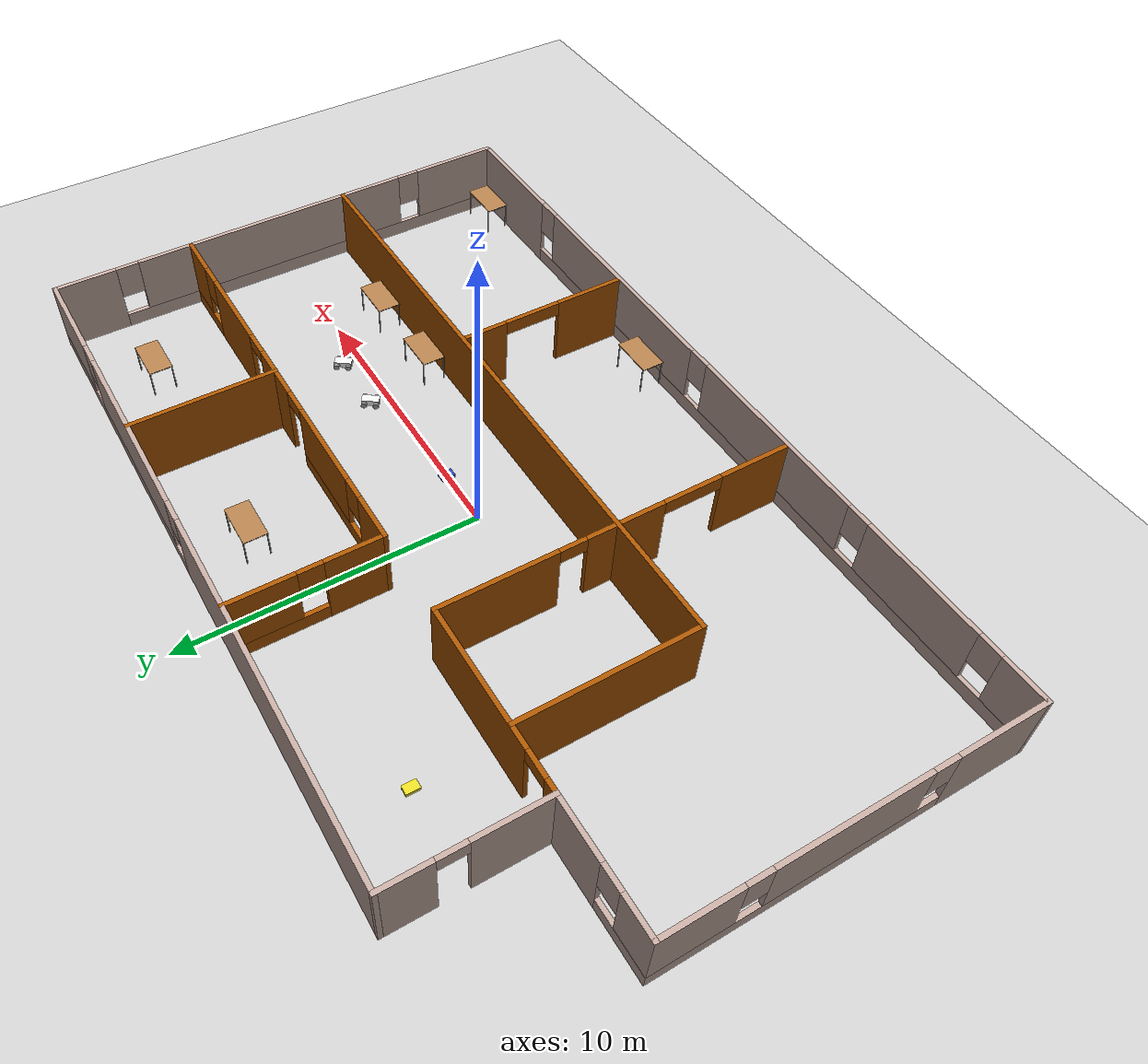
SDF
<sdf version="1.6">
 <world name="default">
  <light name="sun" type="directional">
   <pose>0 0 10 0 -0 0</pose>
   <diffuse>0.8 0.8 0.8 1</diffuse>
   <specular>0.2 0.2 0.2 1</specular>
   <attenuation>
    <range>1000</range>
    <constant>0.9</constant>
    <linear>0.01</linear>
    <quadratic>0.001</quadratic>
   </attenuation>
   <direction>-0.5 0.1 -0.9</direction>
  </light>
  <model name="ground_plane">
   <static>1</static>
   <link name="link">
    <collision name="collision">
     <geometry><plane><normal>0 0 1</normal><size>100 100</size></plane></geometry>
     <surface>
      <contact><collide_bitmask>65535</collide_bitmask></contact>
      <friction><ode><mu>100</mu><mu2>50</mu2></ode></friction>
     </surface>
    </collision>
    <visual name="visual">
     <cast_shadows>0</cast_shadows>
     <geometry><plane><normal>0 0 1</normal><size>100 100</size></plane></geometry>
     <material>
      <script><uri>file://media/materials/scripts/gazebo.material</uri><name>Gazebo/Grey</name></script>
     </material>
    </visual>
   </link>
  </model>
  <gravity>0 0 -9.8</gravity>
  <magnetic_field>6e-06 2.3e-05 -4.2e-05</magnetic_field>
  <atmosphere type="adiabatic"/>
  <physics name="default_physics" default="0" type="ode">
   <max_step_size>0.001</max_step_size>
   <real_time_factor>1</real_time_factor>
   <real_time_update_rate>1000</real_time_update_rate>
  </physics>
  <scene><ambient>0.4 0.4 0.4 1</ambient><background>0.7 0.7 0.7 1</background><shadows>1</shadows></scene>
  <spherical_coordinates>
   <surface_model>EARTH_WGS84</surface_model>
   <latitude_deg>0</latitude_deg>
   <longitude_deg>0</longitude_deg>
   <elevation>0</elevation>
   <heading_deg>0</heading_deg>
  </spherical_coordinates>
  <model name="Building">
   <link name="Wall_11">
    <pose>-1 6 0 0 -0 1.5708</pose>
    <visual name="Wall_11_Visual_0">
     <pose>-1.51661 0 1.25 0 -0 0</pose>
     <geometry><box><size>1.96679 0.15 2.5</size></box></geometry>
     <material>
      <script><uri>file://media/materials/scripts/gazebo.material</uri><name>Gazebo/Grey</name></script>
      <ambient>0.666667 0.333333 0 1</ambient>
     </material>
     <meta><layer>0</layer></meta>
    </visual>
    <collision name="Wall_11_Collision_0">
     <geometry><box><size>1.96679 0.15 2.5</size></box></geometry>
     <pose>-1.51661 0 1.25 0 -0 0</pose>
    </collision>
    <visual name="Wall_11_Visual_1">
     <pose>0.983394 0 0.25 0 -0 0</pose>
     <geometry><box><size>3.03321 0.15 0.5</size></box></geometry>
     <material>
      <script><uri>file://media/materials/scripts/gazebo.material</uri><name>Gazebo/Grey</name></script>
      <ambient>0.666667 0.333333 0 1</ambient>
     </material>
     <meta><layer>0</layer></meta>
    </visual>
    <collision name="Wall_11_Collision_1">
     <geometry><box><size>3.03321 0.15 0.5</size></box></geometry>
     <pose>0.983394 0 0.25 0 -0 0</pose>
    </collision>
    <visual name="Wall_11_Visual_2">
     <pose>1.38339 0 1.5 0 -0 0</pose>
     <geometry><box><size>2.23321 0.15 2</size></box></geometry>
     <material>
      <script><uri>file://media/materials/scripts/gazebo.material</uri><name>Gazebo/Grey</name></script>
      <ambient>0.666667 0.333333 0 1</ambient>
     </material>
     <meta><layer>0</layer></meta>
    </visual>
    <collision name="Wall_11_Collision_2">
     <geometry><box><size>2.23321 0.15 2</size></box></geometry>
     <pose>1.38339 0 1.5 0 -0 0</pose>
    </collision>
    <visual name="Wall_11_Visual_3">
     <pose>-0.133212 0 1.9 0 -0 0</pose>
     <geometry><box><size>0.8 0.15 1.2</size></box></geometry>
     <material>
      <script><uri>file://media/materials/scripts/gazebo.material</uri><name>Gazebo/Grey</name></script>
      <ambient>0.666667 0.333333 0 1</ambient>
     </material>
     <meta><layer>0</layer></meta>
    </visual>
    <collision name="Wall_11_Collision_3">
     <geometry><box><size>0.8 0.15 1.2</size></box></geometry>
     <pose>-0.133212 0 1.9 0 -0 0</pose>
    </collision>
   </link>
   <link name="Wall_13">
    <pose>-12 3.575 0 0 -0 3.14159</pose>
    <visual name="Wall_13_Visual_0">
     <pose>-1.0623 0 1.25 0 -0 0</pose>
     <geometry><box><size>2.02541 0.15 2.5</size></box></geometry>
     <material>
      <script><uri>file://media/materials/scripts/gazebo.material</uri><name>Gazebo/Grey</name></script>
      <ambient>0.760784 0.662745 0.627451 1</ambient>
     </material>
     <meta><layer>0</layer></meta>
    </visual>
    <collision name="Wall_13_Collision_0">
     <geometry><box><size>2.02541 0.15 2.5</size></box></geometry>
     <pose>-1.0623 0 1.25 0 -0 0</pose>
    </collision>
    <visual name="Wall_13_Visual_1">
     <pose>1.0127 0 0.25 0 -0 0</pose>
     <geometry><box><size>2.12459 0.15 0.5</size></box></geometry>
     <material>
      <script><uri>file://media/materials/scripts/gazebo.material</uri><name>Gazebo/Grey</name></script>
      <ambient>0.760784 0.662745 0.627451 1</ambient>
     </material>
     <meta><layer>0</layer></meta>
    </visual>
    <collision name="Wall_13_Collision_1">
     <geometry><box><size>2.12459 0.15 0.5</size></box></geometry>
     <pose>1.0127 0 0.25 0 -0 0</pose>
    </collision>
    <visual name="Wall_13_Visual_2">
     <pose>1.4127 0 1.5 0 -0 0</pose>
     <geometry><box><size>1.32459 0.15 2</size></box></geometry>
     <material>
      <script><uri>file://media/materials/scripts/gazebo.material</uri><name>Gazebo/Grey</name></script>
      <ambient>0.760784 0.662745 0.627451 1</ambient>
     </material>
     <meta><layer>0</layer></meta>
    </visual>
    <collision name="Wall_13_Collision_2">
     <geometry><box><size>1.32459 0.15 2</size></box></geometry>
     <pose>1.4127 0 1.5 0 -0 0</pose>
    </collision>
    <visual name="Wall_13_Visual_3">
     <pose>0.350407 0 1.9 0 -0 0</pose>
     <geometry><box><size>0.8 0.15 1.2</size></box></geometry>
     <material>
      <script><uri>file://media/materials/scripts/gazebo.material</uri><name>Gazebo/Grey</name></script>
      <ambient>0.760784 0.662745 0.627451 1</ambient>
     </material>
     <meta><layer>0</layer></meta>
    </visual>
    <collision name="Wall_13_Collision_3">
     <geometry><box><size>0.8 0.15 1.2</size></box></geometry>
     <pose>0.350407 0 1.9 0 -0 0</pose>
    </collision>
   </link>
   <link name="Wall_15">
    <pose>-10 6 0 0 -0 1.5708</pose>
    <visual name="Wall_15_Visual_0">
     <pose>-1.27093 0 1.25 0 -0 0</pose>
     <geometry><box><size>2.45814 0.15 2.5</size></box></geometry>
     <material>
      <script><uri>file://media/materials/scripts/gazebo.material</uri><name>Gazebo/Grey</name></script>
      <ambient>0.760784 0.662745 0.627451 1</ambient>
     </material>
     <meta><layer>0</layer></meta>
    </visual>
    <collision name="Wall_15_Collision_0">
     <geometry><box><size>2.45814 0.15 2.5</size></box></geometry>
     <pose>-1.27093 0 1.25 0 -0 0</pose>
    </collision>
    <visual name="Wall_15_Visual_1">
     <pose>1.67907 0 1.25 0 -0 0</pose>
     <geometry><box><size>1.64186 0.15 2.5</size></box></geometry>
     <material>
      <script><uri>file://media/materials/scripts/gazebo.material</uri><name>Gazebo/Grey</name></script>
      <ambient>0.760784 0.662745 0.627451 1</ambient>
     </material>
     <meta><layer>0</layer></meta>
    </visual>
    <collision name="Wall_15_Collision_1">
     <geometry><box><size>1.64186 0.15 2.5</size></box></geometry>
     <pose>1.67907 0 1.25 0 -0 0</pose>
    </collision>
    <visual name="Wall_15_Visual_2">
     <pose>0.408138 0 2.25 0 -0 0</pose>
     <geometry><box><size>0.9 0.15 0.5</size></box></geometry>
     <material>
      <script><uri>file://media/materials/scripts/gazebo.material</uri><name>Gazebo/Grey</name></script>
      <ambient>0.760784 0.662745 0.627451 1</ambient>
     </material>
     <meta><layer>0</layer></meta>
    </visual>
    <collision name="Wall_15_Collision_2">
     <geometry><box><size>0.9 0.15 0.5</size></box></geometry>
     <pose>0.408138 0 2.25 0 -0 0</pose>
    </collision>
   </link>
   <link name="Wall_16">
    <pose>2 8.425 0 0 -0 0</pose>
    <visual name="Wall_16_Visual_0">
     <pose>-5.83381 0 1.25 0 -0 0</pose>
     <geometry><box><size>12.4824 0.15 2.5</size></box></geometry>
     <material>
      <script><uri>file://media/materials/scripts/gazebo.material</uri><name>Gazebo/Grey</name></script>
      <ambient>0.760784 0.662745 0.627451 1</ambient>
     </material>
     <meta><layer>0</layer></meta>
    </visual>
    <collision name="Wall_16_Collision_0">
     <geometry><box><size>12.4824 0.15 2.5</size></box></geometry>
     <pose>-5.83381 0 1.25 0 -0 0</pose>
    </collision>
    <visual name="Wall_16_Visual_1">
     <pose>6.24119 0 0.25 0 -0 0</pose>
     <geometry><box><size>11.6676 0.15 0.5</size></box></geometry>
     <material>
      <script><uri>file://media/materials/scripts/gazebo.material</uri><name>Gazebo/Grey</name></script>
      <ambient>0.760784 0.662745 0.627451 1</ambient>
     </material>
     <meta><layer>0</layer></meta>
    </visual>
    <collision name="Wall_16_Collision_1">
     <geometry><box><size>11.6676 0.15 0.5</size></box></geometry>
     <pose>6.24119 0 0.25 0 -0 0</pose>
    </collision>
    <visual name="Wall_16_Visual_2">
     <pose>4.57426 0 1.5 0 -0 0</pose>
     <geometry><box><size>6.73378 0.15 2</size></box></geometry>
     <material>
      <script><uri>file://media/materials/scripts/gazebo.material</uri><name>Gazebo/Grey</name></script>
      <ambient>0.760784 0.662745 0.627451 1</ambient>
     </material>
     <meta><layer>0</layer></meta>
    </visual>
    <collision name="Wall_16_Collision_2">
     <geometry><box><size>6.73378 0.15 2</size></box></geometry>
     <pose>4.57426 0 1.5 0 -0 0</pose>
    </collision>
    <visual name="Wall_16_Visual_3">
     <pose>10.4081 0 1.5 0 -0 0</pose>
     <geometry><box><size>3.33385 0.15 2</size></box></geometry>
     <material>
      <script><uri>file://media/materials/scripts/gazebo.material</uri><name>Gazebo/Grey</name></script>
      <ambient>0.760784 0.662745 0.627451 1</ambient>
     </material>
     <meta><layer>0</layer></meta>
    </visual>
    <collision name="Wall_16_Collision_3">
     <geometry><box><size>3.33385 0.15 2</size></box></geometry>
     <pose>10.4081 0 1.5 0 -0 0</pose>
    </collision>
    <visual name="Wall_16_Visual_4">
     <pose>0.807374 0 1.9 0 -0 0</pose>
     <geometry><box><size>0.8 0.15 1.2</size></box></geometry>
     <material>
      <script><uri>file://media/materials/scripts/gazebo.material</uri><name>Gazebo/Grey</name></script>
      <ambient>0.760784 0.662745 0.627451 1</ambient>
     </material>
     <meta><layer>0</layer></meta>
    </visual>
    <collision name="Wall_16_Collision_4">
     <geometry><box><size>0.8 0.15 1.2</size></box></geometry>
     <pose>0.807374 0 1.9 0 -0 0</pose>
    </collision>
    <visual name="Wall_16_Visual_5">
     <pose>8.34115 0 1.9 0 -0 0</pose>
     <geometry><box><size>0.8 0.15 1.2</size></box></geometry>
     <material>
      <script><uri>file://media/materials/scripts/gazebo.material</uri><name>Gazebo/Grey</name></script>
      <ambient>0.760784 0.662745 0.627451 1</ambient>
     </material>
     <meta><layer>0</layer></meta>
    </visual>
    <collision name="Wall_16_Collision_5">
     <geometry><box><size>0.8 0.15 1.2</size></box></geometry>
     <pose>8.34115 0 1.9 0 -0 0</pose>
    </collision>
   </link>
   <link name="Wall_17">
    <pose>14 0 0 0 0 -1.5708</pose>
    <visual name="Wall_17_Visual_0">
     <pose>-7.40595 0 1.25 0 -0 0</pose>
     <geometry><box><size>2.1881 0.15 2.5</size></box></geometry>
     <material>
      <script><uri>file://media/materials/scripts/gazebo.material</uri><name>Gazebo/Grey</name></script>
      <ambient>0.760784 0.662745 0.627451 1</ambient>
     </material>
     <meta><layer>0</layer></meta>
    </visual>
    <collision name="Wall_17_Collision_0">
     <geometry><box><size>2.1881 0.15 2.5</size></box></geometry>
     <pose>-7.40595 0 1.25 0 -0 0</pose>
    </collision>
    <visual name="Wall_17_Visual_1">
     <pose>1.09405 0 0.25 0 -0 0</pose>
     <geometry><box><size>14.8119 0.15 0.5</size></box></geometry>
     <material>
      <script><uri>file://media/materials/scripts/gazebo.material</uri><name>Gazebo/Grey</name></script>
      <ambient>0.760784 0.662745 0.627451 1</ambient>
     </material>
     <meta><layer>0</layer></meta>
    </visual>
    <collision name="Wall_17_Collision_1">
     <geometry><box><size>14.8119 0.15 0.5</size></box></geometry>
     <pose>1.09405 0 0.25 0 -0 0</pose>
    </collision>
    <visual name="Wall_17_Visual_2">
     <pose>-0.475851 0 1.5 0 -0 0</pose>
     <geometry><box><size>10.0721 0.15 2</size></box></geometry>
     <material>
      <script><uri>file://media/materials/scripts/gazebo.material</uri><name>Gazebo/Grey</name></script>
      <ambient>0.760784 0.662745 0.627451 1</ambient>
     </material>
     <meta><layer>0</layer></meta>
    </visual>
    <collision name="Wall_17_Collision_2">
     <geometry><box><size>10.0721 0.15 2</size></box></geometry>
     <pose>-0.475851 0 1.5 0 -0 0</pose>
    </collision>
    <visual name="Wall_17_Visual_3">
     <pose>6.9301 0 1.5 0 -0 0</pose>
     <geometry><box><size>3.1398 0.15 2</size></box></geometry>
     <material>
      <script><uri>file://media/materials/scripts/gazebo.material</uri><name>Gazebo/Grey</name></script>
      <ambient>0.760784 0.662745 0.627451 1</ambient>
     </material>
     <meta><layer>0</layer></meta>
    </visual>
    <collision name="Wall_17_Collision_3">
     <geometry><box><size>3.1398 0.15 2</size></box></geometry>
     <pose>6.9301 0 1.5 0 -0 0</pose>
    </collision>
    <visual name="Wall_17_Visual_4">
     <pose>-5.9119 0 1.9 0 -0 0</pose>
     <geometry><box><size>0.8 0.15 1.2</size></box></geometry>
     <material>
      <script><uri>file://media/materials/scripts/gazebo.material</uri><name>Gazebo/Grey</name></script>
      <ambient>0.760784 0.662745 0.627451 1</ambient>
     </material>
     <meta><layer>0</layer></meta>
    </visual>
    <collision name="Wall_17_Collision_4">
     <geometry><box><size>0.8 0.15 1.2</size></box></geometry>
     <pose>-5.9119 0 1.9 0 -0 0</pose>
    </collision>
    <visual name="Wall_17_Visual_5">
     <pose>4.9602 0 1.9 0 -0 0</pose>
     <geometry><box><size>0.8 0.15 1.2</size></box></geometry>
     <material>
      <script><uri>file://media/materials/scripts/gazebo.material</uri><name>Gazebo/Grey</name></script>
      <ambient>0.760784 0.662745 0.627451 1</ambient>
     </material>
     <meta><layer>0</layer></meta>
    </visual>
    <collision name="Wall_17_Collision_5">
     <geometry><box><size>0.8 0.15 1.2</size></box></geometry>
     <pose>4.9602 0 1.9 0 -0 0</pose>
    </collision>
   </link>
   <link name="Wall_18">
    <pose>0 -8.425 0 0 -0 3.14159</pose>
    <visual name="Wall_18_Visual_0">
     <pose>-11.979 0 1.25 0 -0 0</pose>
     <geometry><box><size>4.19207 0.15 2.5</size></box></geometry>
     <material>
      <script><uri>file://media/materials/scripts/gazebo.material</uri><name>Gazebo/Grey</name></script>
      <ambient>0.760784 0.662745 0.627451 1</ambient>
     </material>
     <meta><layer>0</layer></meta>
    </visual>
    <collision name="Wall_18_Collision_0">
     <geometry><box><size>4.19207 0.15 2.5</size></box></geometry>
     <pose>-11.979 0 1.25 0 -0 0</pose>
    </collision>
    <visual name="Wall_18_Visual_1">
     <pose>2.09604 0 0.25 0 -0 0</pose>
     <geometry><box><size>23.9579 0.15 0.5</size></box></geometry>
     <material>
      <script><uri>file://media/materials/scripts/gazebo.material</uri><name>Gazebo/Grey</name></script>
      <ambient>0.760784 0.662745 0.627451 1</ambient>
     </material>
     <meta><layer>0</layer></meta>
    </visual>
    <collision name="Wall_18_Collision_1">
     <geometry><box><size>23.9579 0.15 0.5</size></box></geometry>
     <pose>2.09604 0 0.25 0 -0 0</pose>
    </collision>
    <visual name="Wall_18_Visual_2">
     <pose>-4.97168 0 1.5 0 -0 0</pose>
     <geometry><box><size>8.22249 0.15 2</size></box></geometry>
     <material>
      <script><uri>file://media/materials/scripts/gazebo.material</uri><name>Gazebo/Grey</name></script>
      <ambient>0.760784 0.662745 0.627451 1</ambient>
     </material>
     <meta><layer>0</layer></meta>
    </visual>
    <collision name="Wall_18_Collision_2">
     <geometry><box><size>8.22249 0.15 2</size></box></geometry>
     <pose>-4.97168 0 1.5 0 -0 0</pose>
    </collision>
    <visual name="Wall_18_Visual_3">
     <pose>3.2839 0 1.5 0 -0 0</pose>
     <geometry><box><size>6.68867 0.15 2</size></box></geometry>
     <material>
      <script><uri>file://media/materials/scripts/gazebo.material</uri><name>Gazebo/Grey</name></script>
      <ambient>0.760784 0.662745 0.627451 1</ambient>
     </material>
     <meta><layer>0</layer></meta>
    </visual>
    <collision name="Wall_18_Collision_3">
     <geometry><box><size>6.68867 0.15 2</size></box></geometry>
     <pose>3.2839 0 1.5 0 -0 0</pose>
    </collision>
    <visual name="Wall_18_Visual_4">
     <pose>9.55452 0 1.5 0 -0 0</pose>
     <geometry><box><size>4.25259 0.15 2</size></box></geometry>
     <material>
      <script><uri>file://media/materials/scripts/gazebo.material</uri><name>Gazebo/Grey</name></script>
      <ambient>0.760784 0.662745 0.627451 1</ambient>
     </material>
     <meta><layer>0</layer></meta>
    </visual>
    <collision name="Wall_18_Collision_4">
     <geometry><box><size>4.25259 0.15 2</size></box></geometry>
     <pose>9.55452 0 1.5 0 -0 0</pose>
    </collision>
    <visual name="Wall_18_Visual_5">
     <pose>13.2779 0 1.5 0 -0 0</pose>
     <geometry><box><size>1.59418 0.15 2</size></box></geometry>
     <material>
      <script><uri>file://media/materials/scripts/gazebo.material</uri><name>Gazebo/Grey</name></script>
      <ambient>0.760784 0.662745 0.627451 1</ambient>
     </material>
     <meta><layer>0</layer></meta>
    </visual>
    <collision name="Wall_18_Collision_5">
     <geometry><box><size>1.59418 0.15 2</size></box></geometry>
     <pose>13.2779 0 1.5 0 -0 0</pose>
    </collision>
    <visual name="Wall_18_Visual_6">
     <pose>-9.48293 0 1.9 0 -0 0</pose>
     <geometry><box><size>0.8 0.15 1.2</size></box></geometry>
     <material>
      <script><uri>file://media/materials/scripts/gazebo.material</uri><name>Gazebo/Grey</name></script>
      <ambient>0.760784 0.662745 0.627451 1</ambient>
     </material>
     <meta><layer>0</layer></meta>
    </visual>
    <collision name="Wall_18_Collision_6">
     <geometry><box><size>0.8 0.15 1.2</size></box></geometry>
     <pose>-9.48293 0 1.9 0 -0 0</pose>
    </collision>
    <visual name="Wall_18_Visual_7">
     <pose>-0.460437 0 1.9 0 -0 0</pose>
     <geometry><box><size>0.8 0.15 1.2</size></box></geometry>
     <material>
      <script><uri>file://media/materials/scripts/gazebo.material</uri><name>Gazebo/Grey</name></script>
      <ambient>0.760784 0.662745 0.627451 1</ambient>
     </material>
     <meta><layer>0</layer></meta>
    </visual>
    <collision name="Wall_18_Collision_7">
     <geometry><box><size>0.8 0.15 1.2</size></box></geometry>
     <pose>-0.460437 0 1.9 0 -0 0</pose>
    </collision>
    <visual name="Wall_18_Visual_8">
     <pose>7.02823 0 1.9 0 -0 0</pose>
     <geometry><box><size>0.8 0.15 1.2</size></box></geometry>
     <material>
      <script><uri>file://media/materials/scripts/gazebo.material</uri><name>Gazebo/Grey</name></script>
      <ambient>0.760784 0.662745 0.627451 1</ambient>
     </material>
     <meta><layer>0</layer></meta>
    </visual>
    <collision name="Wall_18_Collision_8">
     <geometry><box><size>0.8 0.15 1.2</size></box></geometry>
     <pose>7.02823 0 1.9 0 -0 0</pose>
    </collision>
    <visual name="Wall_18_Visual_9">
     <pose>12.0808 0 1.9 0 -0 0</pose>
     <geometry><box><size>0.8 0.15 1.2</size></box></geometry>
     <material>
      <script><uri>file://media/materials/scripts/gazebo.material</uri><name>Gazebo/Grey</name></script>
      <ambient>0.760784 0.662745 0.627451 1</ambient>
     </material>
     <meta><layer>0</layer></meta>
    </visual>
    <collision name="Wall_18_Collision_9">
     <geometry><box><size>0.8 0.15 1.2</size></box></geometry>
     <pose>12.0808 0 1.9 0 -0 0</pose>
    </collision>
   </link>
   <link name="Wall_19">
    <pose>-14 -2.425 0 0 -0 1.5708</pose>
    <visual name="Wall_19_Visual_0">
     <pose>-4.52766 0 1.25 0 -0 0</pose>
     <geometry><box><size>3.09469 0.15 2.5</size></box></geometry>
     <material>
      <script><uri>file://media/materials/scripts/gazebo.material</uri><name>Gazebo/Grey</name></script>
      <ambient>0.760784 0.662745 0.627451 1</ambient>
     </material>
     <meta><layer>0</layer></meta>
    </visual>
    <collision name="Wall_19_Collision_0">
     <geometry><box><size>3.09469 0.15 2.5</size></box></geometry>
     <pose>-4.52766 0 1.25 0 -0 0</pose>
    </collision>
    <visual name="Wall_19_Visual_1">
     <pose>1.54734 0 0.25 0 -0 0</pose>
     <geometry><box><size>9.05531 0.15 0.5</size></box></geometry>
     <material>
      <script><uri>file://media/materials/scripts/gazebo.material</uri><name>Gazebo/Grey</name></script>
      <ambient>0.760784 0.662745 0.627451 1</ambient>
     </material>
     <meta><layer>0</layer></meta>
    </visual>
    <collision name="Wall_19_Collision_1">
     <geometry><box><size>9.05531 0.15 0.5</size></box></geometry>
     <pose>1.54734 0 0.25 0 -0 0</pose>
    </collision>
    <visual name="Wall_19_Visual_2">
     <pose>0.261773 0 1.5 0 -0 0</pose>
     <geometry><box><size>4.88417 0.15 2</size></box></geometry>
     <material>
      <script><uri>file://media/materials/scripts/gazebo.material</uri><name>Gazebo/Grey</name></script>
      <ambient>0.760784 0.662745 0.627451 1</ambient>
     </material>
     <meta><layer>0</layer></meta>
    </visual>
    <collision name="Wall_19_Collision_2">
     <geometry><box><size>4.88417 0.15 2</size></box></geometry>
     <pose>0.261773 0 1.5 0 -0 0</pose>
    </collision>
    <visual name="Wall_19_Visual_3">
     <pose>4.78943 0 1.5 0 -0 0</pose>
     <geometry><box><size>2.57114 0.15 2</size></box></geometry>
     <material>
      <script><uri>file://media/materials/scripts/gazebo.material</uri><name>Gazebo/Grey</name></script>
      <ambient>0.760784 0.662745 0.627451 1</ambient>
     </material>
     <meta><layer>0</layer></meta>
    </visual>
    <collision name="Wall_19_Collision_3">
     <geometry><box><size>2.57114 0.15 2</size></box></geometry>
     <pose>4.78943 0 1.5 0 -0 0</pose>
    </collision>
    <visual name="Wall_19_Visual_4">
     <pose>-2.58031 0 1.9 0 -0 0</pose>
     <geometry><box><size>0.8 0.15 1.2</size></box></geometry>
     <material>
      <script><uri>file://media/materials/scripts/gazebo.material</uri><name>Gazebo/Grey</name></script>
      <ambient>0.760784 0.662745 0.627451 1</ambient>
     </material>
     <meta><layer>0</layer></meta>
    </visual>
    <collision name="Wall_19_Collision_4">
     <geometry><box><size>0.8 0.15 1.2</size></box></geometry>
     <pose>-2.58031 0 1.9 0 -0 0</pose>
    </collision>
    <visual name="Wall_19_Visual_5">
     <pose>3.10386 0 1.9 0 -0 0</pose>
     <geometry><box><size>0.8 0.15 1.2</size></box></geometry>
     <material>
      <script><uri>file://media/materials/scripts/gazebo.material</uri><name>Gazebo/Grey</name></script>
      <ambient>0.760784 0.662745 0.627451 1</ambient>
     </material>
     <meta><layer>0</layer></meta>
    </visual>
    <collision name="Wall_19_Collision_5">
     <geometry><box><size>0.8 0.15 1.2</size></box></geometry>
     <pose>3.10386 0 1.9 0 -0 0</pose>
    </collision>
   </link>
   <link name="Wall_23">
    <pose>-6.95 3.575 0 0 -0 0</pose>
    <visual name="Wall_23_Visual_0">
     <pose>-2.86366 0 1.25 0 -0 0</pose>
     <geometry><box><size>0.522689 0.15 2.5</size></box></geometry>
     <material>
      <script><uri>file://media/materials/scripts/gazebo.material</uri><name>Gazebo/Grey</name></script>
      <ambient>0.666667 0.333333 0 1</ambient>
     </material>
     <meta><layer>0</layer></meta>
    </visual>
    <collision name="Wall_23_Collision_0">
     <geometry><box><size>0.522689 0.15 2.5</size></box></geometry>
     <pose>-2.86366 0 1.25 0 -0 0</pose>
    </collision>
    <visual name="Wall_23_Visual_1">
     <pose>0.711344 0 1.25 0 -0 0</pose>
     <geometry><box><size>4.82731 0.15 2.5</size></box></geometry>
     <material>
      <script><uri>file://media/materials/scripts/gazebo.material</uri><name>Gazebo/Grey</name></script>
      <ambient>0.666667 0.333333 0 1</ambient>
     </material>
     <meta><layer>0</layer></meta>
    </visual>
    <collision name="Wall_23_Collision_1">
     <geometry><box><size>4.82731 0.15 2.5</size></box></geometry>
     <pose>0.711344 0 1.25 0 -0 0</pose>
    </collision>
    <visual name="Wall_23_Visual_2">
     <pose>-2.15231 0 2.25 0 -0 0</pose>
     <geometry><box><size>0.9 0.15 0.5</size></box></geometry>
     <material>
      <script><uri>file://media/materials/scripts/gazebo.material</uri><name>Gazebo/Grey</name></script>
      <ambient>0.666667 0.333333 0 1</ambient>
     </material>
     <meta><layer>0</layer></meta>
    </visual>
    <collision name="Wall_23_Collision_2">
     <geometry><box><size>0.9 0.15 0.5</size></box></geometry>
     <pose>-2.15231 0 2.25 0 -0 0</pose>
    </collision>
   </link>
   <link name="Wall_24">
    <pose>-3.9 -2.35 0 0 0 -1.5708</pose>
    <visual name="Wall_24_Visual_0">
     <pose>-3.99507 0 1.25 0 -0 0</pose>
     <geometry><box><size>4.00985 0.15 2.5</size></box></geometry>
     <material>
      <script><uri>file://media/materials/scripts/gazebo.material</uri><name>Gazebo/Grey</name></script>
      <ambient>0.666667 0.333333 0 1</ambient>
     </material>
     <meta><layer>0</layer></meta>
    </visual>
    <collision name="Wall_24_Collision_0">
     <geometry><box><size>4.00985 0.15 2.5</size></box></geometry>
     <pose>-3.99507 0 1.25 0 -0 0</pose>
    </collision>
    <visual name="Wall_24_Visual_1">
     <pose>0.23747 0 1.25 0 -0 0</pose>
     <geometry><box><size>2.65523 0.15 2.5</size></box></geometry>
     <material>
      <script><uri>file://media/materials/scripts/gazebo.material</uri><name>Gazebo/Grey</name></script>
      <ambient>0.666667 0.333333 0 1</ambient>
     </material>
     <meta><layer>0</layer></meta>
    </visual>
    <collision name="Wall_24_Collision_1">
     <geometry><box><size>2.65523 0.15 2.5</size></box></geometry>
     <pose>0.23747 0 1.25 0 -0 0</pose>
    </collision>
    <visual name="Wall_24_Visual_2">
     <pose>4.78254 0 1.25 0 -0 0</pose>
     <geometry><box><size>2.43491 0.15 2.5</size></box></geometry>
     <material>
      <script><uri>file://media/materials/scripts/gazebo.material</uri><name>Gazebo/Grey</name></script>
      <ambient>0.666667 0.333333 0 1</ambient>
     </material>
     <meta><layer>0</layer></meta>
    </visual>
    <collision name="Wall_24_Collision_2">
     <geometry><box><size>2.43491 0.15 2.5</size></box></geometry>
     <pose>4.78254 0 1.25 0 -0 0</pose>
    </collision>
    <visual name="Wall_24_Visual_3">
     <pose>-1.54015 0 2.25 0 -0 0</pose>
     <geometry><box><size>0.9 0.15 0.5</size></box></geometry>
     <material>
      <script><uri>file://media/materials/scripts/gazebo.material</uri><name>Gazebo/Grey</name></script>
      <ambient>0.666667 0.333333 0 1</ambient>
     </material>
     <meta><layer>0</layer></meta>
    </visual>
    <collision name="Wall_24_Collision_3">
     <geometry><box><size>0.9 0.15 0.5</size></box></geometry>
     <pose>-1.54015 0 2.25 0 -0 0</pose>
    </collision>
    <visual name="Wall_24_Visual_4">
     <pose>2.56509 0 2.25 0 -0 0</pose>
     <geometry><box><size>2 0.15 0.5</size></box></geometry>
     <material>
      <script><uri>file://media/materials/scripts/gazebo.material</uri><name>Gazebo/Grey</name></script>
      <ambient>0.666667 0.333333 0 1</ambient>
     </material>
     <meta><layer>0</layer></meta>
    </visual>
    <collision name="Wall_24_Collision_4">
     <geometry><box><size>2 0.15 0.5</size></box></geometry>
     <pose>2.56509 0 2.25 0 -0 0</pose>
    </collision>
   </link>
   <link name="Wall_26">
    <collision name="Wall_26_Collision">
     <geometry><box><size>6 0.15 2.5</size></box></geometry>
     <pose>0 0 1.25 0 -0 0</pose>
    </collision>
    <visual name="Wall_26_Visual">
     <pose>0 0 1.25 0 -0 0</pose>
     <geometry><box><size>6 0.15 2.5</size></box></geometry>
     <material>
      <script><uri>file://media/materials/scripts/gazebo.material</uri><name>Gazebo/Grey</name></script>
      <ambient>0.666667 0.333333 0 1</ambient>
     </material>
     <meta><layer>0</layer></meta>
    </visual>
    <pose>-7.87279 0.619488 0 0 0 -1.5708</pose>
   </link>
   <link name="Wall_27">
    <collision name="Wall_27_Collision">
     <geometry><box><size>22 0.15 2.5</size></box></geometry>
     <pose>0 0 1.25 0 -0 0</pose>
    </collision>
    <visual name="Wall_27_Visual">
     <pose>0 0 1.25 0 -0 0</pose>
     <geometry><box><size>22 0.15 2.5</size></box></geometry>
     <material>
      <script><uri>file://media/materials/scripts/gazebo.material</uri><name>Gazebo/Grey</name></script>
      <ambient>0.666667 0.333333 0 1</ambient>
     </material>
     <meta><layer>0</layer></meta>
    </visual>
    <pose>3.05221 -2.30551 0 0 -0 0</pose>
   </link>
   <link name="Wall_29">
    <pose>5 -5.2905 0 0 0 -1.5708</pose>
    <visual name="Wall_29_Visual_0">
     <pose>-2.2125 0 1.25 0 -0 0</pose>
     <geometry><box><size>1.694 0.15 2.5</size></box></geometry>
     <material>
      <script><uri>file://media/materials/scripts/gazebo.material</uri><name>Gazebo/Grey</name></script>
      <ambient>0.666667 0.333333 0 1</ambient>
     </material>
     <meta><layer>0</layer></meta>
    </visual>
    <collision name="Wall_29_Collision_0">
     <geometry><box><size>1.694 0.15 2.5</size></box></geometry>
     <pose>-2.2125 0 1.25 0 -0 0</pose>
    </collision>
    <visual name="Wall_29_Visual_1">
     <pose>1.847 0 1.25 0 -0 0</pose>
     <geometry><box><size>2.425 0.15 2.5</size></box></geometry>
     <material>
      <script><uri>file://media/materials/scripts/gazebo.material</uri><name>Gazebo/Grey</name></script>
      <ambient>0.666667 0.333333 0 1</ambient>
     </material>
     <meta><layer>0</layer></meta>
    </visual>
    <collision name="Wall_29_Collision_1">
     <geometry><box><size>2.425 0.15 2.5</size></box></geometry>
     <pose>1.847 0 1.25 0 -0 0</pose>
    </collision>
    <visual name="Wall_29_Visual_2">
     <pose>-0.3655 0 2.25 0 -0 0</pose>
     <geometry><box><size>2 0.15 0.5</size></box></geometry>
     <material>
      <script><uri>file://media/materials/scripts/gazebo.material</uri><name>Gazebo/Grey</name></script>
      <ambient>0.666667 0.333333 0 1</ambient>
     </material>
     <meta><layer>0</layer></meta>
    </visual>
    <collision name="Wall_29_Collision_2">
     <geometry><box><size>2 0.15 0.5</size></box></geometry>
     <pose>-0.3655 0 2.25 0 -0 0</pose>
    </collision>
   </link>
   <link name="Wall_32">
    <collision name="Wall_32_Collision">
     <geometry><box><size>5 0.15 2.5</size></box></geometry>
     <pose>0 0 1.25 0 -0 0</pose>
    </collision>
    <visual name="Wall_32_Visual">
     <pose>0 0 1.25 0 -0 0</pose>
     <geometry><box><size>5 0.15 2.5</size></box></geometry>
     <material>
      <script><uri>file://media/materials/scripts/gazebo.material</uri><name>Gazebo/Grey</name></script>
      <ambient>0.666667 0.333333 0 1</ambient>
     </material>
     <meta><layer>0</layer></meta>
    </visual>
    <pose>6.64193 5.99105 0 0 -0 1.5708</pose>
   </link>
   <link name="Wall_5">
    <pose>6.5 3.575 0 0 -0 0</pose>
    <visual name="Wall_5_Visual_0">
     <pose>-6.73606 0 1.25 0 -0 0</pose>
     <geometry><box><size>1.67788 0.15 2.5</size></box></geometry>
     <material>
      <script><uri>file://media/materials/scripts/gazebo.material</uri><name>Gazebo/Grey</name></script>
      <ambient>0.666667 0.333333 0 1</ambient>
     </material>
     <meta><layer>0</layer></meta>
    </visual>
    <collision name="Wall_5_Collision_0">
     <geometry><box><size>1.67788 0.15 2.5</size></box></geometry>
     <pose>-6.73606 0 1.25 0 -0 0</pose>
    </collision>
    <visual name="Wall_5_Visual_1">
     <pose>0.119376 0 1.25 0 -0 0</pose>
     <geometry><box><size>2.12253 0.15 2.5</size></box></geometry>
     <material>
      <script><uri>file://media/materials/scripts/gazebo.material</uri><name>Gazebo/Grey</name></script>
      <ambient>0.666667 0.333333 0 1</ambient>
     </material>
     <meta><layer>0</layer></meta>
    </visual>
    <collision name="Wall_5_Collision_1">
     <geometry><box><size>2.12253 0.15 2.5</size></box></geometry>
     <pose>0.119376 0 1.25 0 -0 0</pose>
    </collision>
    <visual name="Wall_5_Visual_2">
     <pose>3.64059 0 1.25 0 -0 0</pose>
     <geometry><box><size>3.1199 0.15 2.5</size></box></geometry>
     <material>
      <script><uri>file://media/materials/scripts/gazebo.material</uri><name>Gazebo/Grey</name></script>
      <ambient>0.666667 0.333333 0 1</ambient>
     </material>
     <meta><layer>0</layer></meta>
    </visual>
    <collision name="Wall_5_Collision_2">
     <geometry><box><size>3.1199 0.15 2.5</size></box></geometry>
     <pose>3.64059 0 1.25 0 -0 0</pose>
    </collision>
    <visual name="Wall_5_Visual_3">
     <pose>-3.86951 0 0.25 0 -0 0</pose>
     <geometry><box><size>4.05523 0.15 0.5</size></box></geometry>
     <material>
      <script><uri>file://media/materials/scripts/gazebo.material</uri><name>Gazebo/Grey</name></script>
      <ambient>0.666667 0.333333 0 1</ambient>
     </material>
     <meta><layer>0</layer></meta>
    </visual>
    <collision name="Wall_5_Collision_3">
     <geometry><box><size>4.05523 0.15 0.5</size></box></geometry>
     <pose>-3.86951 0 0.25 0 -0 0</pose>
    </collision>
    <visual name="Wall_5_Visual_4">
     <pose>6.38777 0 0.25 0 -0 0</pose>
     <geometry><box><size>2.37446 0.15 0.5</size></box></geometry>
     <material>
      <script><uri>file://media/materials/scripts/gazebo.material</uri><name>Gazebo/Grey</name></script>
      <ambient>0.666667 0.333333 0 1</ambient>
     </material>
     <meta><layer>0</layer></meta>
    </visual>
    <collision name="Wall_5_Collision_4">
     <geometry><box><size>2.37446 0.15 0.5</size></box></geometry>
     <pose>6.38777 0 0.25 0 -0 0</pose>
    </collision>
    <visual name="Wall_5_Visual_5">
     <pose>-3.46951 0 1.5 0 -0 0</pose>
     <geometry><box><size>3.25523 0.15 2</size></box></geometry>
     <material>
      <script><uri>file://media/materials/scripts/gazebo.material</uri><name>Gazebo/Grey</name></script>
      <ambient>0.666667 0.333333 0 1</ambient>
     </material>
     <meta><layer>0</layer></meta>
    </visual>
    <collision name="Wall_5_Collision_5">
     <geometry><box><size>3.25523 0.15 2</size></box></geometry>
     <pose>-3.46951 0 1.5 0 -0 0</pose>
    </collision>
    <visual name="Wall_5_Visual_6">
     <pose>-3.46951 0 1.5 0 -0 0</pose>
     <geometry><box><size>3.25523 0.15 2</size></box></geometry>
     <material>
      <script><uri>file://media/materials/scripts/gazebo.material</uri><name>Gazebo/Grey</name></script>
      <ambient>0.666667 0.333333 0 1</ambient>
     </material>
     <meta><layer>0</layer></meta>
    </visual>
    <collision name="Wall_5_Collision_6">
     <geometry><box><size>3.25523 0.15 2</size></box></geometry>
     <pose>-3.46951 0 1.5 0 -0 0</pose>
    </collision>
    <visual name="Wall_5_Visual_7">
     <pose>6.78777 0 1.5 0 -0 0</pose>
     <geometry><box><size>1.57446 0.15 2</size></box></geometry>
     <material>
      <script><uri>file://media/materials/scripts/gazebo.material</uri><name>Gazebo/Grey</name></script>
      <ambient>0.666667 0.333333 0 1</ambient>
     </material>
     <meta><layer>0</layer></meta>
    </visual>
    <collision name="Wall_5_Collision_7">
     <geometry><box><size>1.57446 0.15 2</size></box></geometry>
     <pose>6.78777 0 1.5 0 -0 0</pose>
    </collision>
    <visual name="Wall_5_Visual_8">
     <pose>-5.49712 0 1.9 0 -0 0</pose>
     <geometry><box><size>0.8 0.15 1.2</size></box></geometry>
     <material>
      <script><uri>file://media/materials/scripts/gazebo.material</uri><name>Gazebo/Grey</name></script>
      <ambient>0.666667 0.333333 0 1</ambient>
     </material>
     <meta><layer>0</layer></meta>
    </visual>
    <collision name="Wall_5_Collision_8">
     <geometry><box><size>0.8 0.15 1.2</size></box></geometry>
     <pose>-5.49712 0 1.9 0 -0 0</pose>
    </collision>
    <visual name="Wall_5_Visual_9">
     <pose>5.60054 0 1.9 0 -0 0</pose>
     <geometry><box><size>0.8 0.15 1.2</size></box></geometry>
     <material>
      <script><uri>file://media/materials/scripts/gazebo.material</uri><name>Gazebo/Grey</name></script>
      <ambient>0.666667 0.333333 0 1</ambient>
     </material>
     <meta><layer>0</layer></meta>
    </visual>
    <collision name="Wall_5_Collision_9">
     <geometry><box><size>0.8 0.15 1.2</size></box></geometry>
     <pose>5.60054 0 1.9 0 -0 0</pose>
    </collision>
    <visual name="Wall_5_Visual_10">
     <pose>1.63064 0 2.25 0 -0 0</pose>
     <geometry><box><size>0.9 0.15 0.5</size></box></geometry>
     <material>
      <script><uri>file://media/materials/scripts/gazebo.material</uri><name>Gazebo/Grey</name></script>
      <ambient>0.666667 0.333333 0 1</ambient>
     </material>
     <meta><layer>0</layer></meta>
    </visual>
    <collision name="Wall_5_Collision_10">
     <geometry><box><size>0.9 0.15 0.5</size></box></geometry>
     <pose>1.63064 0 2.25 0 -0 0</pose>
    </collision>
    <visual name="Wall_5_Visual_11">
     <pose>-1.39189 0 2.25 0 -0 0</pose>
     <geometry><box><size>0.9 0.15 0.5</size></box></geometry>
     <material>
      <script><uri>file://media/materials/scripts/gazebo.material</uri><name>Gazebo/Grey</name></script>
      <ambient>0.666667 0.333333 0 1</ambient>
     </material>
     <meta><layer>0</layer></meta>
    </visual>
    <collision name="Wall_5_Collision_11">
     <geometry><box><size>0.9 0.15 0.5</size></box></geometry>
     <pose>-1.39189 0 2.25 0 -0 0</pose>
    </collision>
    <visual name="Wall_5_Visual_12">
     <pose>-1.39189 0 2.25 0 -0 0</pose>
     <geometry><box><size>0.9 0.15 0.5</size></box></geometry>
     <material>
      <script><uri>file://media/materials/scripts/gazebo.material</uri><name>Gazebo/Grey</name></script>
      <ambient>0.666667 0.333333 0 1</ambient>
     </material>
     <meta><layer>0</layer></meta>
    </visual>
    <collision name="Wall_5_Collision_12">
     <geometry><box><size>0.9 0.15 0.5</size></box></geometry>
     <pose>-1.39189 0 2.25 0 -0 0</pose>
    </collision>
   </link>
   <static>1</static>
  </model>
  <model name="MobileRobot">
   <link name="link_1">
    <pose>6.56986 0.243352 0.109995 1.57004 1.5524 0.455973</pose>
    <inertial>
     <mass>1</mass>
     <inertia><ixx>0.145833</ixx><ixy>0</ixy><ixz>0</ixz><iyy>0.145833</iyy><iyz>0</iyz><izz>0.125</izz></inertia>
    </inertial>
    <visual name="visual">
     <geometry><cylinder><radius>0.1</radius><length>0.1</length></cylinder></geometry>
     <material>
      <lighting>1</lighting>
      <script><uri>file://media/materials/scripts/gazebo.material</uri><name>Gazebo/Grey</name></script>
      <shader type="pixel"><normal_map>__default__</normal_map></shader>
      <ambient>0 0 0 1</ambient>
      <diffuse>0.7 0.7 0.7 1</diffuse>
      <specular>0.01 0.01 0.01 1</specular>
      <emissive>0 0 0 1</emissive>
     </material>
    </visual>
    <collision name="collision">
     <geometry><cylinder><radius>0.1</radius><length>0.1</length></cylinder></geometry>
     <surface>
      <friction>
       <ode><mu>1</mu><mu2>1</mu2><fdir1>0 0 0</fdir1><slip1>0</slip1><slip2>0</slip2></ode>
       <torsional>
        <coefficient>1</coefficient>
        <patch_radius>0</patch_radius>
        <surface_radius>0</surface_radius>
        <use_patch_radius>1</use_patch_radius>
        <ode><slip>0</slip></ode>
       </torsional>
      </friction>
      <bounce><restitution_coefficient>0</restitution_coefficient><threshold>1e+06</threshold></bounce>
      <contact>
       <collide_without_contact>0</collide_without_contact>
       <collide_without_contact_bitmask>1</collide_without_contact_bitmask>
       <collide_bitmask>1</collide_bitmask>
       <ode>
        <soft_cfm>0</soft_cfm>
        <soft_erp>0.2</soft_erp>
        <kp>1e+13</kp>
        <kd>1</kd>
        <max_vel>0.01</max_vel>
        <min_depth>0</min_depth>
       </ode>
       <bullet>
        <split_impulse>1</split_impulse>
        <split_impulse_penetration_threshold>-0.01</split_impulse_penetration_threshold>
        <soft_cfm>0</soft_cfm>
        <soft_erp>0.2</soft_erp>
        <kp>1e+13</kp>
        <kd>1</kd>
       </bullet>
      </contact>
     </surface>
    </collision>
   </link>
   <link name="link_1_clone">
    <pose>6.21083 0.067016 0.099992 1.57078 0.110851 0.45737</pose>
    <inertial>
     <mass>1</mass>
     <inertia><ixx>0.145833</ixx><ixy>0</ixy><ixz>0</ixz><iyy>0.145833</iyy><iyz>0</iyz><izz>0.125</izz></inertia>
    </inertial>
    <visual name="visual">
     <geometry><cylinder><radius>0.1</radius><length>0.1</length></cylinder></geometry>
     <material>
      <lighting>1</lighting>
      <script><uri>file://media/materials/scripts/gazebo.material</uri><name>Gazebo/Grey</name></script>
      <shader type="pixel"><normal_map>__default__</normal_map></shader>
      <ambient>0 0 0 1</ambient>
      <diffuse>0.7 0.7 0.7 1</diffuse>
      <specular>0.01 0.01 0.01 1</specular>
      <emissive>0 0 0 1</emissive>
     </material>
    </visual>
    <collision name="collision">
     <geometry><cylinder><radius>0.1</radius><length>0.1</length></cylinder></geometry>
     <surface>
      <friction>
       <ode><mu>1</mu><mu2>1</mu2><fdir1>0 0 0</fdir1><slip1>0</slip1><slip2>0</slip2></ode>
       <torsional>
        <coefficient>1</coefficient>
        <patch_radius>0</patch_radius>
        <surface_radius>0</surface_radius>
        <use_patch_radius>1</use_patch_radius>
        <ode><slip>0</slip></ode>
       </torsional>
      </friction>
      <bounce><restitution_coefficient>0</restitution_coefficient><threshold>1e+06</threshold></bounce>
      <contact>
       <collide_without_contact>0</collide_without_contact>
       <collide_without_contact_bitmask>1</collide_without_contact_bitmask>
       <collide_bitmask>1</collide_bitmask>
       <ode>
        <soft_cfm>0</soft_cfm>
        <soft_erp>0.2</soft_erp>
        <kp>1e+13</kp>
        <kd>1</kd>
        <max_vel>0.01</max_vel>
        <min_depth>0</min_depth>
       </ode>
       <bullet>
        <split_impulse>1</split_impulse>
        <split_impulse_penetration_threshold>-0.01</split_impulse_penetration_threshold>
        <soft_cfm>0</soft_cfm>
        <soft_erp>0.2</soft_erp>
        <kp>1e+13</kp>
        <kd>1</kd>
       </bullet>
      </contact>
     </surface>
    </collision>
   </link>
   <link name="link_1_clone_0">
    <pose>6.74629 -0.115713 0.100001 -1.57078 0.76703 -2.68421</pose>
    <inertial>
     <mass>1</mass>
     <inertia><ixx>0.145833</ixx><ixy>0</ixy><ixz>0</ixz><iyy>0.145833</iyy><iyz>0</iyz><izz>0.125</izz></inertia>
    </inertial>
    <visual name="visual">
     <geometry><cylinder><radius>0.1</radius><length>0.1</length></cylinder></geometry>
     <material>
      <lighting>1</lighting>
      <script><uri>file://media/materials/scripts/gazebo.material</uri><name>Gazebo/Grey</name></script>
      <shader type="pixel"><normal_map>__default__</normal_map></shader>
      <ambient>0 0 0 1</ambient>
      <diffuse>0.7 0.7 0.7 1</diffuse>
      <specular>0.01 0.01 0.01 1</specular>
      <emissive>0 0 0 1</emissive>
     </material>
    </visual>
    <collision name="collision">
     <geometry><cylinder><radius>0.1</radius><length>0.1</length></cylinder></geometry>
     <surface>
      <friction>
       <ode><mu>1</mu><mu2>1</mu2><fdir1>0 0 0</fdir1><slip1>0</slip1><slip2>0</slip2></ode>
       <torsional>
        <coefficient>1</coefficient>
        <patch_radius>0</patch_radius>
        <surface_radius>0</surface_radius>
        <use_patch_radius>1</use_patch_radius>
        <ode><slip>0</slip></ode>
       </torsional>
      </friction>
      <bounce><restitution_coefficient>0</restitution_coefficient><threshold>1e+06</threshold></bounce>
      <contact>
       <collide_without_contact>0</collide_without_contact>
       <collide_without_contact_bitmask>1</collide_without_contact_bitmask>
       <collide_bitmask>1</collide_bitmask>
       <ode>
        <soft_cfm>0</soft_cfm>
        <soft_erp>0.2</soft_erp>
        <kp>1e+13</kp>
        <kd>1</kd>
        <max_vel>0.01</max_vel>
        <min_depth>0</min_depth>
       </ode>
       <bullet>
        <split_impulse>1</split_impulse>
        <split_impulse_penetration_threshold>-0.01</split_impulse_penetration_threshold>
        <soft_cfm>0</soft_cfm>
        <soft_erp>0.2</soft_erp>
        <kp>1e+13</kp>
        <kd>1</kd>
       </bullet>
      </contact>
     </surface>
    </collision>
   </link>
   <link name="link_1_clone_1">
    <pose>6.38729 -0.292109 0.099998 -1.57076 1.15777 -2.68419</pose>
    <inertial>
     <mass>1</mass>
     <inertia><ixx>0.145833</ixx><ixy>0</ixy><ixz>0</ixz><iyy>0.145833</iyy><iyz>0</iyz><izz>0.125</izz></inertia>
    </inertial>
    <visual name="visual">
     <geometry><cylinder><radius>0.1</radius><length>0.1</length></cylinder></geometry>
     <material>
      <lighting>1</lighting>
      <script><uri>file://media/materials/scripts/gazebo.material</uri><name>Gazebo/Grey</name></script>
      <shader type="pixel"><normal_map>__default__</normal_map></shader>
      <ambient>0 0 0 1</ambient>
      <diffuse>0.7 0.7 0.7 1</diffuse>
      <specular>0.01 0.01 0.01 1</specular>
      <emissive>0 0 0 1</emissive>
     </material>
    </visual>
    <collision name="collision">
     <geometry><cylinder><radius>0.1</radius><length>0.1</length></cylinder></geometry>
     <surface>
      <friction>
       <ode><mu>1</mu><mu2>1</mu2><fdir1>0 0 0</fdir1><slip1>0</slip1><slip2>0</slip2></ode>
       <torsional>
        <coefficient>1</coefficient>
        <patch_radius>0</patch_radius>
        <surface_radius>0</surface_radius>
        <use_patch_radius>1</use_patch_radius>
        <ode><slip>0</slip></ode>
       </torsional>
      </friction>
      <bounce><restitution_coefficient>0</restitution_coefficient><threshold>1e+06</threshold></bounce>
      <contact>
       <collide_without_contact>0</collide_without_contact>
       <collide_without_contact_bitmask>1</collide_without_contact_bitmask>
       <collide_bitmask>1</collide_bitmask>
       <ode>
        <soft_cfm>0</soft_cfm>
        <soft_erp>0.2</soft_erp>
        <kp>1e+13</kp>
        <kd>1</kd>
        <max_vel>0.01</max_vel>
        <min_depth>0</min_depth>
       </ode>
       <bullet>
        <split_impulse>1</split_impulse>
        <split_impulse_penetration_threshold>-0.01</split_impulse_penetration_threshold>
        <soft_cfm>0</soft_cfm>
        <soft_erp>0.2</soft_erp>
        <kp>1e+13</kp>
        <kd>1</kd>
       </bullet>
      </contact>
     </surface>
    </collision>
   </link>
   <link name="link_3">
    <pose>6.47856 -0.024348 0.149996 -1.4e-05 -8e-06 0.4567</pose>
    <inertial>
     <mass>1</mass>
     <inertia>
      <ixx>0.166667</ixx>
      <ixy>0</ixy>
      <ixz>0</ixz>
      <iyy>0.166667</iyy>
      <iyz>0</iyz>
      <izz>0.166667</izz>
     </inertia>
    </inertial>
    <visual name="visual">
     <geometry><box><size>0.6 0.3 0.2</size></box></geometry>
     <material>
      <lighting>1</lighting>
      <script><uri>file://media/materials/scripts/gazebo.material</uri><name>Gazebo/White</name></script>
      <shader type="pixel"><normal_map>__default__</normal_map></shader>
      <ambient>0.0 0.7 0.7 1</ambient>
      <diffuse>0.7 0.7 0.7 1</diffuse>
      <specular>0.01 0.01 0.01 1</specular>
      <emissive>0 0 0 1</emissive>
     </material>
    </visual>
    <collision name="collision">
     <geometry><box><size>0.6 0.3 0.2</size></box></geometry>
     <surface>
      <friction>
       <ode><mu>1</mu><mu2>1</mu2><fdir1>0 0 0</fdir1><slip1>0</slip1><slip2>0</slip2></ode>
       <torsional>
        <coefficient>1</coefficient>
        <patch_radius>0</patch_radius>
        <surface_radius>0</surface_radius>
        <use_patch_radius>1</use_patch_radius>
        <ode><slip>0</slip></ode>
       </torsional>
      </friction>
      <bounce><restitution_coefficient>0</restitution_coefficient><threshold>1e+06</threshold></bounce>
      <contact>
       <collide_without_contact>0</collide_without_contact>
       <collide_without_contact_bitmask>1</collide_without_contact_bitmask>
       <collide_bitmask>1</collide_bitmask>
       <ode>
        <soft_cfm>0</soft_cfm>
        <soft_erp>0.2</soft_erp>
        <kp>1e+13</kp>
        <kd>1</kd>
        <max_vel>0.01</max_vel>
        <min_depth>0</min_depth>
       </ode>
       <bullet>
        <split_impulse>1</split_impulse>
        <split_impulse_penetration_threshold>-0.01</split_impulse_penetration_threshold>
        <soft_cfm>0</soft_cfm>
        <soft_erp>0.2</soft_erp>
        <kp>1e+13</kp>
        <kd>1</kd>
       </bullet>
      </contact>
     </surface>
    </collision>
   </link>
   <joint name="link_3_JOINT_1" type="revolute">
    <parent>link_3</parent>
    <child>link_1_clone</child>
    <axis>
     <xyz>0 0 1</xyz>
     <use_parent_model_frame>0</use_parent_model_frame>
     <limit>
      <lower>-1.79769e+308</lower>
      <upper>1.79769e+308</upper>
      <effort>-1</effort>
      <velocity>-1</velocity>
     </limit>
     <dynamics>
      <spring_reference>0</spring_reference>
      <spring_stiffness>0</spring_stiffness>
      <damping>0</damping>
      <friction>0</friction>
     </dynamics>
    </axis>
    <physics>
     <ode><limit><cfm>0</cfm><erp>0.2</erp></limit><suspension><cfm>0</cfm><erp>0.2</erp></suspension></ode>
    </physics>
   </joint>
   <joint name="link_3_JOINT_2" type="revolute">
    <parent>link_3</parent>
    <child>link_1</child>
    <axis>
     <xyz>0 0 1</xyz>
     <use_parent_model_frame>0</use_parent_model_frame>
     <limit>
      <lower>-1.79769e+308</lower>
      <upper>1.79769e+308</upper>
      <effort>-1</effort>
      <velocity>-1</velocity>
     </limit>
     <dynamics>
      <spring_reference>0</spring_reference>
      <spring_stiffness>0</spring_stiffness>
      <damping>0</damping>
      <friction>0</friction>
     </dynamics>
    </axis>
    <physics>
     <ode><limit><cfm>0</cfm><erp>0.2</erp></limit><suspension><cfm>0</cfm><erp>0.2</erp></suspension></ode>
    </physics>
   </joint>
   <joint name="link_3_JOINT_3" type="revolute">
    <parent>link_3</parent>
    <child>link_1_clone_0</child>
    <axis>
     <xyz>0 0 1</xyz>
     <use_parent_model_frame>0</use_parent_model_frame>
     <limit>
      <lower>-1.79769e+308</lower>
      <upper>1.79769e+308</upper>
      <effort>-1</effort>
      <velocity>-1</velocity>
     </limit>
     <dynamics>
      <spring_reference>0</spring_reference>
      <spring_stiffness>0</spring_stiffness>
      <damping>0</damping>
      <friction>0</friction>
     </dynamics>
    </axis>
    <physics>
     <ode><limit><cfm>0</cfm><erp>0.2</erp></limit><suspension><cfm>0</cfm><erp>0.2</erp></suspension></ode>
    </physics>
   </joint>
   <joint name="link_3_JOINT_4" type="revolute">
    <parent>link_3</parent>
    <child>link_1_clone_1</child>
    <axis>
     <xyz>0 0 1</xyz>
     <use_parent_model_frame>0</use_parent_model_frame>
     <limit>
      <lower>-1.79769e+308</lower>
      <upper>1.79769e+308</upper>
      <effort>-1</effort>
      <velocity>-1</velocity>
     </limit>
     <dynamics>
      <spring_reference>0</spring_reference>
      <spring_stiffness>0</spring_stiffness>
      <damping>0</damping>
      <friction>0</friction>
     </dynamics>
    </axis>
    <physics>
     <ode><limit><cfm>0</cfm><erp>0.2</erp></limit><suspension><cfm>0</cfm><erp>0.2</erp></suspension></ode>
    </physics>
   </joint>
   <static>0</static>
   <pose>2.594970 -2.492684 -0.115614 0.008507 -0.017288 0.505325</pose>
  </model>
  <model name="MobileRobot_0">
   <link name="link_1">
    <pose>4.60881 0.240898 0.11 1.57078 1.55257 0.459419</pose>
    <inertial>
     <mass>1</mass>
     <inertia><ixx>0.145833</ixx><ixy>0</ixy><ixz>0</ixz><iyy>0.145833</iyy><iyz>0</iyz><izz>0.125</izz></inertia>
    </inertial>
    <visual name="visual">
     <geometry><cylinder><radius>0.1</radius><length>0.1</length></cylinder></geometry>
     <material>
      <lighting>1</lighting>
      <script><uri>file://media/materials/scripts/gazebo.material</uri><name>Gazebo/Grey</name></script>
      <shader type="pixel"><normal_map>__default__</normal_map></shader>
      <ambient>0 0 0 1</ambient>
      <diffuse>0.7 0.7 0.7 1</diffuse>
      <specular>0.01 0.01 0.01 1</specular>
      <emissive>0 0 0 1</emissive>
     </material>
    </visual>
    <collision name="collision">
     <geometry><cylinder><radius>0.1</radius><length>0.1</length></cylinder></geometry>
     <surface>
      <friction>
       <ode><mu>1</mu><mu2>1</mu2><fdir1>0 0 0</fdir1><slip1>0</slip1><slip2>0</slip2></ode>
       <torsional>
        <coefficient>1</coefficient>
        <patch_radius>0</patch_radius>
        <surface_radius>0</surface_radius>
        <use_patch_radius>1</use_patch_radius>
        <ode><slip>0</slip></ode>
       </torsional>
      </friction>
      <bounce><restitution_coefficient>0</restitution_coefficient><threshold>1e+06</threshold></bounce>
      <contact>
       <collide_without_contact>0</collide_without_contact>
       <collide_without_contact_bitmask>1</collide_without_contact_bitmask>
       <collide_bitmask>1</collide_bitmask>
       <ode>
        <soft_cfm>0</soft_cfm>
        <soft_erp>0.2</soft_erp>
        <kp>1e+13</kp>
        <kd>1</kd>
        <max_vel>0.01</max_vel>
        <min_depth>0</min_depth>
       </ode>
       <bullet>
        <split_impulse>1</split_impulse>
        <split_impulse_penetration_threshold>-0.01</split_impulse_penetration_threshold>
        <soft_cfm>0</soft_cfm>
        <soft_erp>0.2</soft_erp>
        <kp>1e+13</kp>
        <kd>1</kd>
       </bullet>
      </contact>
     </surface>
    </collision>
   </link>
   <link name="link_1_clone">
    <pose>4.25025 0.063593 0.1 1.5708 0.106267 0.460072</pose>
    <inertial>
     <mass>1</mass>
     <inertia><ixx>0.145833</ixx><ixy>0</ixy><ixz>0</ixz><iyy>0.145833</iyy><iyz>0</iyz><izz>0.125</izz></inertia>
    </inertial>
    <visual name="visual">
     <geometry><cylinder><radius>0.1</radius><length>0.1</length></cylinder></geometry>
     <material>
      <lighting>1</lighting>
      <script><uri>file://media/materials/scripts/gazebo.material</uri><name>Gazebo/Grey</name></script>
      <shader type="pixel"><normal_map>__default__</normal_map></shader>
      <ambient>0 0 0 1</ambient>
      <diffuse>0.7 0.7 0.7 1</diffuse>
      <specular>0.01 0.01 0.01 1</specular>
      <emissive>0 0 0 1</emissive>
     </material>
    </visual>
    <collision name="collision">
     <geometry><cylinder><radius>0.1</radius><length>0.1</length></cylinder></geometry>
     <surface>
      <friction>
       <ode><mu>1</mu><mu2>1</mu2><fdir1>0 0 0</fdir1><slip1>0</slip1><slip2>0</slip2></ode>
       <torsional>
        <coefficient>1</coefficient>
        <patch_radius>0</patch_radius>
        <surface_radius>0</surface_radius>
        <use_patch_radius>1</use_patch_radius>
        <ode><slip>0</slip></ode>
       </torsional>
      </friction>
      <bounce><restitution_coefficient>0</restitution_coefficient><threshold>1e+06</threshold></bounce>
      <contact>
       <collide_without_contact>0</collide_without_contact>
       <collide_without_contact_bitmask>1</collide_without_contact_bitmask>
       <collide_bitmask>1</collide_bitmask>
       <ode>
        <soft_cfm>0</soft_cfm>
        <soft_erp>0.2</soft_erp>
        <kp>1e+13</kp>
        <kd>1</kd>
        <max_vel>0.01</max_vel>
        <min_depth>0</min_depth>
       </ode>
       <bullet>
        <split_impulse>1</split_impulse>
        <split_impulse_penetration_threshold>-0.01</split_impulse_penetration_threshold>
        <soft_cfm>0</soft_cfm>
        <soft_erp>0.2</soft_erp>
        <kp>1e+13</kp>
        <kd>1</kd>
       </bullet>
      </contact>
     </surface>
    </collision>
   </link>
   <link name="link_1_clone_0">
    <pose>4.7862 -0.11769 0.1 -1.5708 0.764191 -2.68152</pose>
    <inertial>
     <mass>1</mass>
     <inertia><ixx>0.145833</ixx><ixy>0</ixy><ixz>0</ixz><iyy>0.145833</iyy><iyz>0</iyz><izz>0.125</izz></inertia>
    </inertial>
    <visual name="visual">
     <geometry><cylinder><radius>0.1</radius><length>0.1</length></cylinder></geometry>
     <material>
      <lighting>1</lighting>
      <script><uri>file://media/materials/scripts/gazebo.material</uri><name>Gazebo/Grey</name></script>
      <shader type="pixel"><normal_map>__default__</normal_map></shader>
      <ambient>0 0 0 1</ambient>
      <diffuse>0.7 0.7 0.7 1</diffuse>
      <specular>0.01 0.01 0.01 1</specular>
      <emissive>0 0 0 1</emissive>
     </material>
    </visual>
    <collision name="collision">
     <geometry><cylinder><radius>0.1</radius><length>0.1</length></cylinder></geometry>
     <surface>
      <friction>
       <ode><mu>1</mu><mu2>1</mu2><fdir1>0 0 0</fdir1><slip1>0</slip1><slip2>0</slip2></ode>
       <torsional>
        <coefficient>1</coefficient>
        <patch_radius>0</patch_radius>
        <surface_radius>0</surface_radius>
        <use_patch_radius>1</use_patch_radius>
        <ode><slip>0</slip></ode>
       </torsional>
      </friction>
      <bounce><restitution_coefficient>0</restitution_coefficient><threshold>1e+06</threshold></bounce>
      <contact>
       <collide_without_contact>0</collide_without_contact>
       <collide_without_contact_bitmask>1</collide_without_contact_bitmask>
       <collide_bitmask>1</collide_bitmask>
       <ode>
        <soft_cfm>0</soft_cfm>
        <soft_erp>0.2</soft_erp>
        <kp>1e+13</kp>
        <kd>1</kd>
        <max_vel>0.01</max_vel>
        <min_depth>0</min_depth>
       </ode>
       <bullet>
        <split_impulse>1</split_impulse>
        <split_impulse_penetration_threshold>-0.01</split_impulse_penetration_threshold>
        <soft_cfm>0</soft_cfm>
        <soft_erp>0.2</soft_erp>
        <kp>1e+13</kp>
        <kd>1</kd>
       </bullet>
      </contact>
     </surface>
    </collision>
   </link>
   <link name="link_1_clone_1">
    <pose>4.42767 -0.295054 0.1 -1.5708 1.14063 -2.68152</pose>
    <inertial>
     <mass>1</mass>
     <inertia><ixx>0.145833</ixx><ixy>0</ixy><ixz>0</ixz><iyy>0.145833</iyy><iyz>0</iyz><izz>0.125</izz></inertia>
    </inertial>
    <visual name="visual">
     <geometry><cylinder><radius>0.1</radius><length>0.1</length></cylinder></geometry>
     <material>
      <lighting>1</lighting>
      <script><uri>file://media/materials/scripts/gazebo.material</uri><name>Gazebo/Grey</name></script>
      <shader type="pixel"><normal_map>__default__</normal_map></shader>
      <ambient>0 0 0 1</ambient>
      <diffuse>0.7 0.7 0.7 1</diffuse>
      <specular>0.01 0.01 0.01 1</specular>
      <emissive>0 0 0 1</emissive>
     </material>
    </visual>
    <collision name="collision">
     <geometry><cylinder><radius>0.1</radius><length>0.1</length></cylinder></geometry>
     <surface>
      <friction>
       <ode><mu>1</mu><mu2>1</mu2><fdir1>0 0 0</fdir1><slip1>0</slip1><slip2>0</slip2></ode>
       <torsional>
        <coefficient>1</coefficient>
        <patch_radius>0</patch_radius>
        <surface_radius>0</surface_radius>
        <use_patch_radius>1</use_patch_radius>
        <ode><slip>0</slip></ode>
       </torsional>
      </friction>
      <bounce><restitution_coefficient>0</restitution_coefficient><threshold>1e+06</threshold></bounce>
      <contact>
       <collide_without_contact>0</collide_without_contact>
       <collide_without_contact_bitmask>1</collide_without_contact_bitmask>
       <collide_bitmask>1</collide_bitmask>
       <ode>
        <soft_cfm>0</soft_cfm>
        <soft_erp>0.2</soft_erp>
        <kp>1e+13</kp>
        <kd>1</kd>
        <max_vel>0.01</max_vel>
        <min_depth>0</min_depth>
       </ode>
       <bullet>
        <split_impulse>1</split_impulse>
        <split_impulse_penetration_threshold>-0.01</split_impulse_penetration_threshold>
        <soft_cfm>0</soft_cfm>
        <soft_erp>0.2</soft_erp>
        <kp>1e+13</kp>
        <kd>1</kd>
       </bullet>
      </contact>
     </surface>
    </collision>
   </link>
   <link name="link_3">
    <pose>4.51822 -0.027048 0.15 0 -0 0.459401</pose>
    <inertial>
     <mass>1</mass>
     <inertia>
      <ixx>0.166667</ixx>
      <ixy>0</ixy>
      <ixz>0</ixz>
      <iyy>0.166667</iyy>
      <iyz>0</iyz>
      <izz>0.166667</izz>
     </inertia>
    </inertial>
    <visual name="visual">
     <geometry><box><size>0.6 0.3 0.2</size></box></geometry>
     <material>
      <lighting>1</lighting>
      <script><uri>file://media/materials/scripts/gazebo.material</uri><name>Gazebo/White</name></script>
      <shader type="pixel"><normal_map>__default__</normal_map></shader>
      <ambient>0.0 0.7 0.7 1</ambient>
      <diffuse>0.7 0.7 0.7 1</diffuse>
      <specular>0.01 0.01 0.01 1</specular>
      <emissive>0 0 0 1</emissive>
     </material>
    </visual>
    <collision name="collision">
     <geometry><box><size>0.6 0.3 0.2</size></box></geometry>
     <surface>
      <friction>
       <ode><mu>1</mu><mu2>1</mu2><fdir1>0 0 0</fdir1><slip1>0</slip1><slip2>0</slip2></ode>
       <torsional>
        <coefficient>1</coefficient>
        <patch_radius>0</patch_radius>
        <surface_radius>0</surface_radius>
        <use_patch_radius>1</use_patch_radius>
        <ode><slip>0</slip></ode>
       </torsional>
      </friction>
      <bounce><restitution_coefficient>0</restitution_coefficient><threshold>1e+06</threshold></bounce>
      <contact>
       <collide_without_contact>0</collide_without_contact>
       <collide_without_contact_bitmask>1</collide_without_contact_bitmask>
       <collide_bitmask>1</collide_bitmask>
       <ode>
        <soft_cfm>0</soft_cfm>
        <soft_erp>0.2</soft_erp>
        <kp>1e+13</kp>
        <kd>1</kd>
        <max_vel>0.01</max_vel>
        <min_depth>0</min_depth>
       </ode>
       <bullet>
        <split_impulse>1</split_impulse>
        <split_impulse_penetration_threshold>-0.01</split_impulse_penetration_threshold>
        <soft_cfm>0</soft_cfm>
        <soft_erp>0.2</soft_erp>
        <kp>1e+13</kp>
        <kd>1</kd>
       </bullet>
      </contact>
     </surface>
    </collision>
   </link>
   <joint name="link_3_JOINT_1" type="revolute">
    <parent>link_3</parent>
    <child>link_1_clone</child>
    <axis>
     <xyz>0 0 1</xyz>
     <use_parent_model_frame>0</use_parent_model_frame>
     <limit>
      <lower>-1.79769e+308</lower>
      <upper>1.79769e+308</upper>
      <effort>-1</effort>
      <velocity>-1</velocity>
     </limit>
     <dynamics>
      <spring_reference>0</spring_reference>
      <spring_stiffness>0</spring_stiffness>
      <damping>0</damping>
      <friction>0</friction>
     </dynamics>
    </axis>
    <physics>
     <ode><limit><cfm>0</cfm><erp>0.2</erp></limit><suspension><cfm>0</cfm><erp>0.2</erp></suspension></ode>
    </physics>
   </joint>
   <joint name="link_3_JOINT_2" type="revolute">
    <parent>link_3</parent>
    <child>link_1</child>
    <axis>
     <xyz>0 0 1</xyz>
     <use_parent_model_frame>0</use_parent_model_frame>
     <limit>
      <lower>-1.79769e+308</lower>
      <upper>1.79769e+308</upper>
      <effort>-1</effort>
      <velocity>-1</velocity>
     </limit>
     <dynamics>
      <spring_reference>0</spring_reference>
      <spring_stiffness>0</spring_stiffness>
      <damping>0</damping>
      <friction>0</friction>
     </dynamics>
    </axis>
    <physics>
     <ode><limit><cfm>0</cfm><erp>0.2</erp></limit><suspension><cfm>0</cfm><erp>0.2</erp></suspension></ode>
    </physics>
   </joint>
   <joint name="link_3_JOINT_3" type="revolute">
    <parent>link_3</parent>
    <child>link_1_clone_0</child>
    <axis>
     <xyz>0 0 1</xyz>
     <use_parent_model_frame>0</use_parent_model_frame>
     <limit>
      <lower>-1.79769e+308</lower>
      <upper>1.79769e+308</upper>
      <effort>-1</effort>
      <velocity>-1</velocity>
     </limit>
     <dynamics>
      <spring_reference>0</spring_reference>
      <spring_stiffness>0</spring_stiffness>
      <damping>0</damping>
      <friction>0</friction>
     </dynamics>
    </axis>
    <physics>
     <ode><limit><cfm>0</cfm><erp>0.2</erp></limit><suspension><cfm>0</cfm><erp>0.2</erp></suspension></ode>
    </physics>
   </joint>
   <joint name="link_3_JOINT_4" type="revolute">
    <parent>link_3</parent>
    <child>link_1_clone_1</child>
    <axis>
     <xyz>0 0 1</xyz>
     <use_parent_model_frame>0</use_parent_model_frame>
     <limit>
      <lower>-1.79769e+308</lower>
      <upper>1.79769e+308</upper>
      <effort>-1</effort>
      <velocity>-1</velocity>
     </limit>
     <dynamics>
      <spring_reference>0</spring_reference>
      <spring_stiffness>0</spring_stiffness>
      <damping>0</damping>
      <friction>0</friction>
     </dynamics>
    </axis>
    <physics>
     <ode><limit><cfm>0</cfm><erp>0.2</erp></limit><suspension><cfm>0</cfm><erp>0.2</erp></suspension></ode>
    </physics>
   </joint>
   <static>0</static>
   <pose>2.246079 -1.634734 -0.148984 0.015603 -0.031530 0.531844</pose>
  </model>
  <model name="table">
   <static>1</static>
   <link name="link">
    <collision name="surface">
     <pose>0 0 1 0 -0 0</pose>
     <geometry><box><size>1.5 0.8 0.03</size></box></geometry>
     <surface><friction><ode><mu>0.6</mu><mu2>0.6</mu2></ode></friction></surface>
    </collision>
    <visual name="visual1">
     <pose>0 0 1 0 -0 0</pose>
     <geometry><box><size>1.5 0.8 0.03</size></box></geometry>
     <material>
      <script><uri>file://media/materials/scripts/gazebo.material</uri><name>Gazebo/Wood</name></script>
     </material>
    </visual>
    <collision name="front_left_leg">
     <pose>0.68 0.38 0.5 0 -0 0</pose>
     <geometry><cylinder><radius>0.02</radius><length>1</length></cylinder></geometry>
    </collision>
    <visual name="front_left_leg">
     <pose>0.68 0.38 0.5 0 -0 0</pose>
     <geometry><cylinder><radius>0.02</radius><length>1</length></cylinder></geometry>
     <material>
      <script><uri>file://media/materials/scripts/gazebo.material</uri><name>Gazebo/Grey</name></script>
     </material>
    </visual>
    <collision name="front_right_leg">
     <pose>0.68 -0.38 0.5 0 -0 0</pose>
     <geometry><cylinder><radius>0.02</radius><length>1</length></cylinder></geometry>
    </collision>
    <visual name="front_right_leg">
     <pose>0.68 -0.38 0.5 0 -0 0</pose>
     <geometry><cylinder><radius>0.02</radius><length>1</length></cylinder></geometry>
     <material>
      <script><uri>file://media/materials/scripts/gazebo.material</uri><name>Gazebo/Grey</name></script>
     </material>
    </visual>
    <collision name="back_right_leg">
     <pose>-0.68 -0.38 0.5 0 -0 0</pose>
     <geometry><cylinder><radius>0.02</radius><length>1</length></cylinder></geometry>
    </collision>
    <visual name="back_right_leg">
     <pose>-0.68 -0.38 0.5 0 -0 0</pose>
     <geometry><cylinder><radius>0.02</radius><length>1</length></cylinder></geometry>
     <material>
      <script><uri>file://media/materials/scripts/gazebo.material</uri><name>Gazebo/Grey</name></script>
     </material>
    </visual>
    <collision name="back_left_leg">
     <pose>-0.68 0.38 0.5 0 -0 0</pose>
     <geometry><cylinder><radius>0.02</radius><length>1</length></cylinder></geometry>
    </collision>
    <visual name="back_left_leg">
     <pose>-0.68 0.38 0.5 0 -0 0</pose>
     <geometry><cylinder><radius>0.02</radius><length>1</length></cylinder></geometry>
     <material>
      <script><uri>file://media/materials/scripts/gazebo.material</uri><name>Gazebo/Grey</name></script>
     </material>
    </visual>
   </link>
   <pose>9.8632 -1.64363 0 0 0 0</pose>
  </model>
  <model name="table_0">
   <static>1</static>
   <link name="link">
    <collision name="surface">
     <pose>0 0 1 0 -0 0</pose>
     <geometry><box><size>1.5 0.8 0.03</size></box></geometry>
     <surface><friction><ode><mu>0.6</mu><mu2>0.6</mu2></ode></friction></surface>
    </collision>
    <visual name="visual1">
     <pose>0 0 1 0 -0 0</pose>
     <geometry><box><size>1.5 0.8 0.03</size></box></geometry>
     <material>
      <script><uri>file://media/materials/scripts/gazebo.material</uri><name>Gazebo/Wood</name></script>
     </material>
    </visual>
    <collision name="front_left_leg">
     <pose>0.68 0.38 0.5 0 -0 0</pose>
     <geometry><cylinder><radius>0.02</radius><length>1</length></cylinder></geometry>
    </collision>
    <visual name="front_left_leg">
     <pose>0.68 0.38 0.5 0 -0 0</pose>
     <geometry><cylinder><radius>0.02</radius><length>1</length></cylinder></geometry>
     <material>
      <script><uri>file://media/materials/scripts/gazebo.material</uri><name>Gazebo/Grey</name></script>
     </material>
    </visual>
    <collision name="front_right_leg">
     <pose>0.68 -0.38 0.5 0 -0 0</pose>
     <geometry><cylinder><radius>0.02</radius><length>1</length></cylinder></geometry>
    </collision>
    <visual name="front_right_leg">
     <pose>0.68 -0.38 0.5 0 -0 0</pose>
     <geometry><cylinder><radius>0.02</radius><length>1</length></cylinder></geometry>
     <material>
      <script><uri>file://media/materials/scripts/gazebo.material</uri><name>Gazebo/Grey</name></script>
     </material>
    </visual>
    <collision name="back_right_leg">
     <pose>-0.68 -0.38 0.5 0 -0 0</pose>
     <geometry><cylinder><radius>0.02</radius><length>1</length></cylinder></geometry>
    </collision>
    <visual name="back_right_leg">
     <pose>-0.68 -0.38 0.5 0 -0 0</pose>
     <geometry><cylinder><radius>0.02</radius><length>1</length></cylinder></geometry>
     <material>
      <script><uri>file://media/materials/scripts/gazebo.material</uri><name>Gazebo/Grey</name></script>
     </material>
    </visual>
    <collision name="back_left_leg">
     <pose>-0.68 0.38 0.5 0 -0 0</pose>
     <geometry><cylinder><radius>0.02</radius><length>1</length></cylinder></geometry>
    </collision>
    <visual name="back_left_leg">
     <pose>-0.68 0.38 0.5 0 -0 0</pose>
     <geometry><cylinder><radius>0.02</radius><length>1</length></cylinder></geometry>
     <material>
      <script><uri>file://media/materials/scripts/gazebo.material</uri><name>Gazebo/Grey</name></script>
     </material>
    </visual>
   </link>
   <pose>6.70251 -1.71681 0 0 0 0</pose>
  </model>
  <model name="table_1">
   <static>1</static>
   <link name="link">
    <collision name="surface">
     <pose>0 0 1 0 -0 0</pose>
     <geometry><box><size>1.5 0.8 0.03</size></box></geometry>
     <surface><friction><ode><mu>0.6</mu><mu2>0.6</mu2></ode></friction></surface>
    </collision>
    <visual name="visual1">
     <pose>0 0 1 0 -0 0</pose>
     <geometry><box><size>1.5 0.8 0.03</size></box></geometry>
     <material>
      <script><uri>file://media/materials/scripts/gazebo.material</uri><name>Gazebo/Wood</name></script>
     </material>
    </visual>
    <collision name="front_left_leg">
     <pose>0.68 0.38 0.5 0 -0 0</pose>
     <geometry><cylinder><radius>0.02</radius><length>1</length></cylinder></geometry>
    </collision>
    <visual name="front_left_leg">
     <pose>0.68 0.38 0.5 0 -0 0</pose>
     <geometry><cylinder><radius>0.02</radius><length>1</length></cylinder></geometry>
     <material>
      <script><uri>file://media/materials/scripts/gazebo.material</uri><name>Gazebo/Grey</name></script>
     </material>
    </visual>
    <collision name="front_right_leg">
     <pose>0.68 -0.38 0.5 0 -0 0</pose>
     <geometry><cylinder><radius>0.02</radius><length>1</length></cylinder></geometry>
    </collision>
    <visual name="front_right_leg">
     <pose>0.68 -0.38 0.5 0 -0 0</pose>
     <geometry><cylinder><radius>0.02</radius><length>1</length></cylinder></geometry>
     <material>
      <script><uri>file://media/materials/scripts/gazebo.material</uri><name>Gazebo/Grey</name></script>
     </material>
    </visual>
    <collision name="back_right_leg">
     <pose>-0.68 -0.38 0.5 0 -0 0</pose>
     <geometry><cylinder><radius>0.02</radius><length>1</length></cylinder></geometry>
    </collision>
    <visual name="back_right_leg">
     <pose>-0.68 -0.38 0.5 0 -0 0</pose>
     <geometry><cylinder><radius>0.02</radius><length>1</length></cylinder></geometry>
     <material>
      <script><uri>file://media/materials/scripts/gazebo.material</uri><name>Gazebo/Grey</name></script>
     </material>
    </visual>
    <collision name="back_left_leg">
     <pose>-0.68 0.38 0.5 0 -0 0</pose>
     <geometry><cylinder><radius>0.02</radius><length>1</length></cylinder></geometry>
    </collision>
    <visual name="back_left_leg">
     <pose>-0.68 0.38 0.5 0 -0 0</pose>
     <geometry><cylinder><radius>0.02</radius><length>1</length></cylinder></geometry>
     <material>
      <script><uri>file://media/materials/scripts/gazebo.material</uri><name>Gazebo/Grey</name></script>
     </material>
    </visual>
   </link>
   <pose>10.8177 6.39215 0 0 0 0</pose>
  </model>
  <model name="table_2">
   <static>1</static>
   <link name="link">
    <collision name="surface">
     <pose>0 0 1 0 -0 0</pose>
     <geometry><box><size>1.5 0.8 0.03</size></box></geometry>
     <surface><friction><ode><mu>0.6</mu><mu2>0.6</mu2></ode></friction></surface>
    </collision>
    <visual name="visual1">
     <pose>0 0 1 0 -0 0</pose>
     <geometry><box><size>1.5 0.8 0.03</size></box></geometry>
     <material>
      <script><uri>file://media/materials/scripts/gazebo.material</uri><name>Gazebo/Wood</name></script>
     </material>
    </visual>
    <collision name="front_left_leg">
     <pose>0.68 0.38 0.5 0 -0 0</pose>
     <geometry><cylinder><radius>0.02</radius><length>1</length></cylinder></geometry>
    </collision>
    <visual name="front_left_leg">
     <pose>0.68 0.38 0.5 0 -0 0</pose>
     <geometry><cylinder><radius>0.02</radius><length>1</length></cylinder></geometry>
     <material>
      <script><uri>file://media/materials/scripts/gazebo.material</uri><name>Gazebo/Grey</name></script>
     </material>
    </visual>
    <collision name="front_right_leg">
     <pose>0.68 -0.38 0.5 0 -0 0</pose>
     <geometry><cylinder><radius>0.02</radius><length>1</length></cylinder></geometry>
    </collision>
    <visual name="front_right_leg">
     <pose>0.68 -0.38 0.5 0 -0 0</pose>
     <geometry><cylinder><radius>0.02</radius><length>1</length></cylinder></geometry>
     <material>
      <script><uri>file://media/materials/scripts/gazebo.material</uri><name>Gazebo/Grey</name></script>
     </material>
    </visual>
    <collision name="back_right_leg">
     <pose>-0.68 -0.38 0.5 0 -0 0</pose>
     <geometry><cylinder><radius>0.02</radius><length>1</length></cylinder></geometry>
    </collision>
    <visual name="back_right_leg">
     <pose>-0.68 -0.38 0.5 0 -0 0</pose>
     <geometry><cylinder><radius>0.02</radius><length>1</length></cylinder></geometry>
     <material>
      <script><uri>file://media/materials/scripts/gazebo.material</uri><name>Gazebo/Grey</name></script>
     </material>
    </visual>
    <collision name="back_left_leg">
     <pose>-0.68 0.38 0.5 0 -0 0</pose>
     <geometry><cylinder><radius>0.02</radius><length>1</length></cylinder></geometry>
    </collision>
    <visual name="back_left_leg">
     <pose>-0.68 0.38 0.5 0 -0 0</pose>
     <geometry><cylinder><radius>0.02</radius><length>1</length></cylinder></geometry>
     <material>
      <script><uri>file://media/materials/scripts/gazebo.material</uri><name>Gazebo/Grey</name></script>
     </material>
    </visual>
   </link>
   <pose>2.60762 6.45728 0 0 0 0</pose>
  </model>
  <model name="table_3">
   <static>1</static>
   <link name="link">
    <collision name="surface">
     <pose>0 0 1 0 -0 0</pose>
     <geometry><box><size>1.5 0.8 0.03</size></box></geometry>
     <surface><friction><ode><mu>0.6</mu><mu2>0.6</mu2></ode></friction></surface>
    </collision>
    <visual name="visual1">
     <pose>0 0 1 0 -0 0</pose>
     <geometry><box><size>1.5 0.8 0.03</size></box></geometry>
     <material>
      <script><uri>file://media/materials/scripts/gazebo.material</uri><name>Gazebo/Wood</name></script>
     </material>
    </visual>
    <collision name="front_left_leg">
     <pose>0.68 0.38 0.5 0 -0 0</pose>
     <geometry><cylinder><radius>0.02</radius><length>1</length></cylinder></geometry>
    </collision>
    <visual name="front_left_leg">
     <pose>0.68 0.38 0.5 0 -0 0</pose>
     <geometry><cylinder><radius>0.02</radius><length>1</length></cylinder></geometry>
     <material>
      <script><uri>file://media/materials/scripts/gazebo.material</uri><name>Gazebo/Grey</name></script>
     </material>
    </visual>
    <collision name="front_right_leg">
     <pose>0.68 -0.38 0.5 0 -0 0</pose>
     <geometry><cylinder><radius>0.02</radius><length>1</length></cylinder></geometry>
    </collision>
    <visual name="front_right_leg">
     <pose>0.68 -0.38 0.5 0 -0 0</pose>
     <geometry><cylinder><radius>0.02</radius><length>1</length></cylinder></geometry>
     <material>
      <script><uri>file://media/materials/scripts/gazebo.material</uri><name>Gazebo/Grey</name></script>
     </material>
    </visual>
    <collision name="back_right_leg">
     <pose>-0.68 -0.38 0.5 0 -0 0</pose>
     <geometry><cylinder><radius>0.02</radius><length>1</length></cylinder></geometry>
    </collision>
    <visual name="back_right_leg">
     <pose>-0.68 -0.38 0.5 0 -0 0</pose>
     <geometry><cylinder><radius>0.02</radius><length>1</length></cylinder></geometry>
     <material>
      <script><uri>file://media/materials/scripts/gazebo.material</uri><name>Gazebo/Grey</name></script>
     </material>
    </visual>
    <collision name="back_left_leg">
     <pose>-0.68 0.38 0.5 0 -0 0</pose>
     <geometry><cylinder><radius>0.02</radius><length>1</length></cylinder></geometry>
    </collision>
    <visual name="back_left_leg">
     <pose>-0.68 0.38 0.5 0 -0 0</pose>
     <geometry><cylinder><radius>0.02</radius><length>1</length></cylinder></geometry>
     <material>
      <script><uri>file://media/materials/scripts/gazebo.material</uri><name>Gazebo/Grey</name></script>
     </material>
    </visual>
   </link>
   <pose>12.9713 -7.86462 0 0 0 0</pose>
  </model>
  <model name="table_4">
   <static>1</static>
   <link name="link">
    <collision name="surface">
     <pose>0 0 1 0 -0 0</pose>
     <geometry><box><size>1.5 0.8 0.03</size></box></geometry>
     <surface><friction><ode><mu>0.6</mu><mu2>0.6</mu2></ode></friction></surface>
    </collision>
    <visual name="visual1">
     <pose>0 0 1 0 -0 0</pose>
     <geometry><box><size>1.5 0.8 0.03</size></box></geometry>
     <material>
      <script><uri>file://media/materials/scripts/gazebo.material</uri><name>Gazebo/Wood</name></script>
     </material>
    </visual>
    <collision name="front_left_leg">
     <pose>0.68 0.38 0.5 0 -0 0</pose>
     <geometry><cylinder><radius>0.02</radius><length>1</length></cylinder></geometry>
    </collision>
    <visual name="front_left_leg">
     <pose>0.68 0.38 0.5 0 -0 0</pose>
     <geometry><cylinder><radius>0.02</radius><length>1</length></cylinder></geometry>
     <material>
      <script><uri>file://media/materials/scripts/gazebo.material</uri><name>Gazebo/Grey</name></script>
     </material>
    </visual>
    <collision name="front_right_leg">
     <pose>0.68 -0.38 0.5 0 -0 0</pose>
     <geometry><cylinder><radius>0.02</radius><length>1</length></cylinder></geometry>
    </collision>
    <visual name="front_right_leg">
     <pose>0.68 -0.38 0.5 0 -0 0</pose>
     <geometry><cylinder><radius>0.02</radius><length>1</length></cylinder></geometry>
     <material>
      <script><uri>file://media/materials/scripts/gazebo.material</uri><name>Gazebo/Grey</name></script>
     </material>
    </visual>
    <collision name="back_right_leg">
     <pose>-0.68 -0.38 0.5 0 -0 0</pose>
     <geometry><cylinder><radius>0.02</radius><length>1</length></cylinder></geometry>
    </collision>
    <visual name="back_right_leg">
     <pose>-0.68 -0.38 0.5 0 -0 0</pose>
     <geometry><cylinder><radius>0.02</radius><length>1</length></cylinder></geometry>
     <material>
      <script><uri>file://media/materials/scripts/gazebo.material</uri><name>Gazebo/Grey</name></script>
     </material>
    </visual>
    <collision name="back_left_leg">
     <pose>-0.68 0.38 0.5 0 -0 0</pose>
     <geometry><cylinder><radius>0.02</radius><length>1</length></cylinder></geometry>
    </collision>
    <visual name="back_left_leg">
     <pose>-0.68 0.38 0.5 0 -0 0</pose>
     <geometry><cylinder><radius>0.02</radius><length>1</length></cylinder></geometry>
     <material>
      <script><uri>file://media/materials/scripts/gazebo.material</uri><name>Gazebo/Grey</name></script>
     </material>
    </visual>
   </link>
   <pose>2.82273 -7.93919 0 0 0 0</pose>
  </model>
  <model name="unit_box_1">
   <pose>8.5 5.5 0.06 0 0 1.5708</pose>
   <link name="link">
    <inertial>
     <mass>1</mass>
     <inertia>
      <ixx>0.0416667</ixx>
      <ixy>0</ixy>
      <ixz>0</ixz>
      <iyy>0.0566667</iyy>
      <iyz>0</iyz>
      <izz>0.0683333</izz>
     </inertia>
    </inertial>
    <collision name="collision">
     <geometry><box><size>0.3 0.45 0.12</size></box></geometry>
     <surface>
      <friction><ode><mu>1</mu><mu2>1</mu2></ode></friction>
      <contact><ode><kp>1e+07</kp><kd>1</kd><min_depth>0.001</min_depth><max_vel>0.1</max_vel></ode></contact>
     </surface>
    </collision>
    <visual name="visual">
     <geometry><box><size>0.3 0.45 0.12</size></box></geometry>
     <material>
      <lighting>1</lighting>
      <script><uri>file://media/materials/scripts/gazebo.material</uri><name>Gazebo/Yellow</name></script>
      <shader type="pixel"><normal_map>__default__</normal_map></shader>
      <ambient>0.6 0.5 0.3 1</ambient>
      <diffuse>0.6 0.5 0.3 1</diffuse>
      <specular>0.01 0.01 0.01 1</specular>
      <emissive>0 0 0 1</emissive>
     </material>
    </visual>
   </link>
  </model>
  <model name="unit_box_2">
   <pose>1.885 0.12 0.1325 0 0 0</pose>
   <link name="link">
    <inertial>
     <mass>0.05</mass>
     <inertia>
      <ixx>0.016667</ixx>
      <ixy>0</ixy>
      <ixz>0</ixz>
      <iyy>0.016667</iyy>
      <iyz>0</iyz>
      <izz>0.016667</izz>
     </inertia>
    </inertial>
    <collision name="collision">
     <geometry><box><size>0.015 0.025 0.025</size></box></geometry>
     <surface>
      <friction>
       <ode><mu>50</mu><mu2>50</mu2></ode>
       <torsional><ode><coefficient>10</coefficient><use_patch_radius>true</use_patch_radius></ode></torsional>
      </friction>
      <contact><ode><kp>1e+06</kp><kd>150</kd><min_depth>0.001</min_depth><max_vel>0.1</max_vel></ode></contact>
     </surface>
    </collision>
    <visual name="visual">
     <geometry><box><size>0.015 0.025 0.025</size></box></geometry>
     <material>
      <lighting>1</lighting>
      <script><uri>file://media/materials/scripts/gazebo.material</uri><name>Gazebo/Red</name></script>
      <shader type="pixel"><normal_map>__default__</normal_map></shader>
      <ambient>0.9 0.1 0.1 1</ambient>
      <diffuse>0.9 0.1 0.1 1</diffuse>
      <specular>0.01 0.01 0.01 1</specular>
      <emissive>0 0 0 1</emissive>
     </material>
    </visual>
   </link>
  </model>
  <model name="unit_box_3">
   <pose>2.0 0 0.06 0 0 0</pose>
   <link name="link">
    <inertial>
     <mass>1</mass>
     <inertia>
      <ixx>0.0416667</ixx>
      <ixy>0</ixy>
      <ixz>0</ixz>
      <iyy>0.0566667</iyy>
      <iyz>0</iyz>
      <izz>0.0683333</izz>
     </inertia>
    </inertial>
    <collision name="collision">
     <geometry><box><size>0.3 0.45 0.12</size></box></geometry>
     <surface>
      <friction><ode><mu>1</mu><mu2>1</mu2></ode></friction>
      <contact><ode><kp>1e+07</kp><kd>1</kd><min_depth>0.001</min_depth><max_vel>0.1</max_vel></ode></contact>
     </surface>
    </collision>
    <visual name="visual">
     <geometry><box><size>0.3 0.45 0.12</size></box></geometry>
     <material>
      <lighting>1</lighting>
      <script><uri>file://media/materials/scripts/gazebo.material</uri><name>Gazebo/Blue</name></script>
      <shader type="pixel"><normal_map>__default__</normal_map></shader>
      <ambient>0.1 0.3 0.7 1</ambient>
      <diffuse>0.1 0.3 0.7 1</diffuse>
      <specular>0.01 0.01 0.01 1</specular>
      <emissive>0 0 0 1</emissive>
     </material>
    </visual>
   </link>
  </model>
  <model name="unit_box_4">
   <pose>-7 6.0 0.06 0 0 0</pose>
   <link name="link">
    <inertial>
     <mass>1</mass>
     <inertia>
      <ixx>0.0416667</ixx>
      <ixy>0</ixy>
      <ixz>0</ixz>
      <iyy>0.0566667</iyy>
      <iyz>0</iyz>
      <izz>0.0683333</izz>
     </inertia>
    </inertial>
    <collision name="collision">
     <geometry><box><size>0.3 0.45 0.12</size></box></geometry>
     <surface>
      <friction><ode><mu>1</mu><mu2>1</mu2></ode></friction>
      <contact><ode><kp>1e+07</kp><kd>1</kd><min_depth>0.001</min_depth><max_vel>0.1</max_vel></ode></contact>
     </surface>
    </collision>
    <visual name="visual">
     <geometry><box><size>0.3 0.45 0.12</size></box></geometry>
     <material>
      <lighting>1</lighting>
      <script><uri>file://media/materials/scripts/gazebo.material</uri><name>Gazebo/Yellow</name></script>
      <shader type="pixel"><normal_map>__default__</normal_map></shader>
      <ambient>0.6 0.5 0.3 1</ambient>
      <diffuse>0.6 0.5 0.3 1</diffuse>
      <specular>0.01 0.01 0.01 1</specular>
      <emissive>0 0 0 1</emissive>
     </material>
    </visual>
   </link>
  </model>
 </world>
</sdf>
